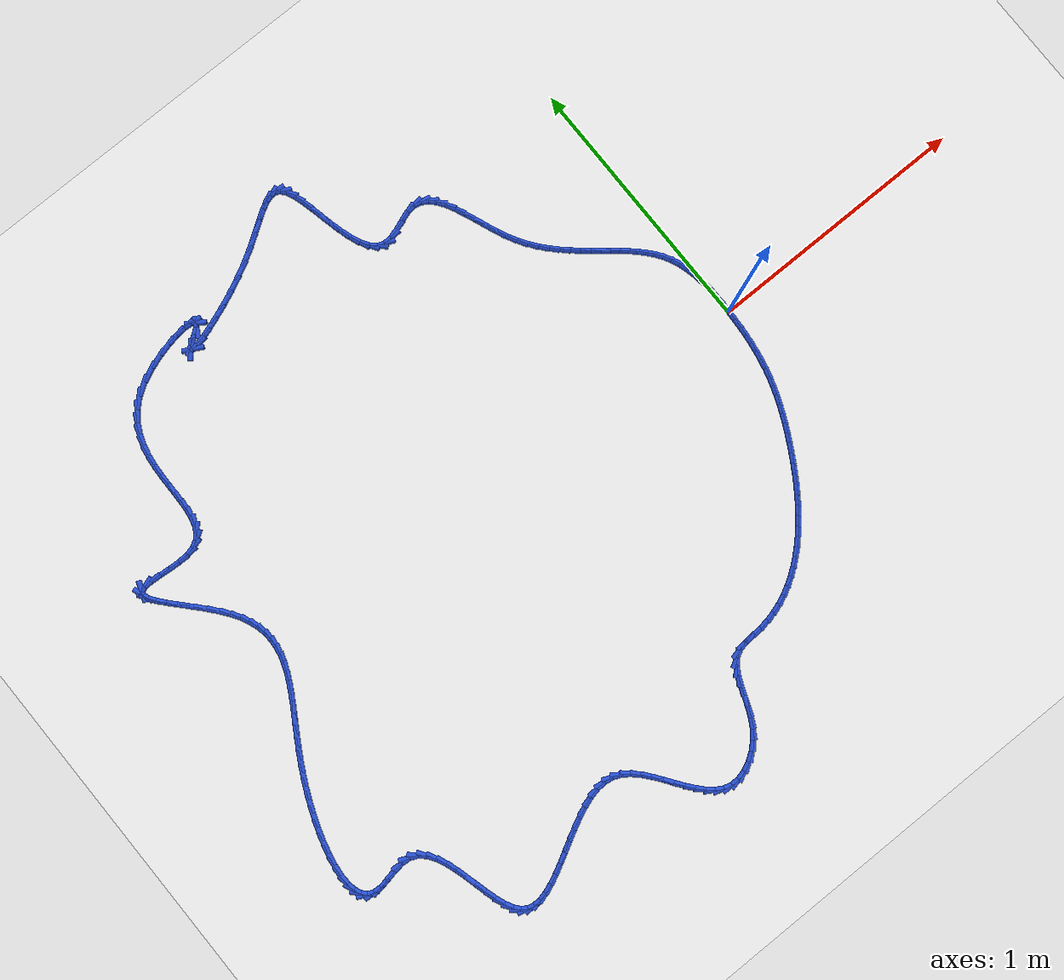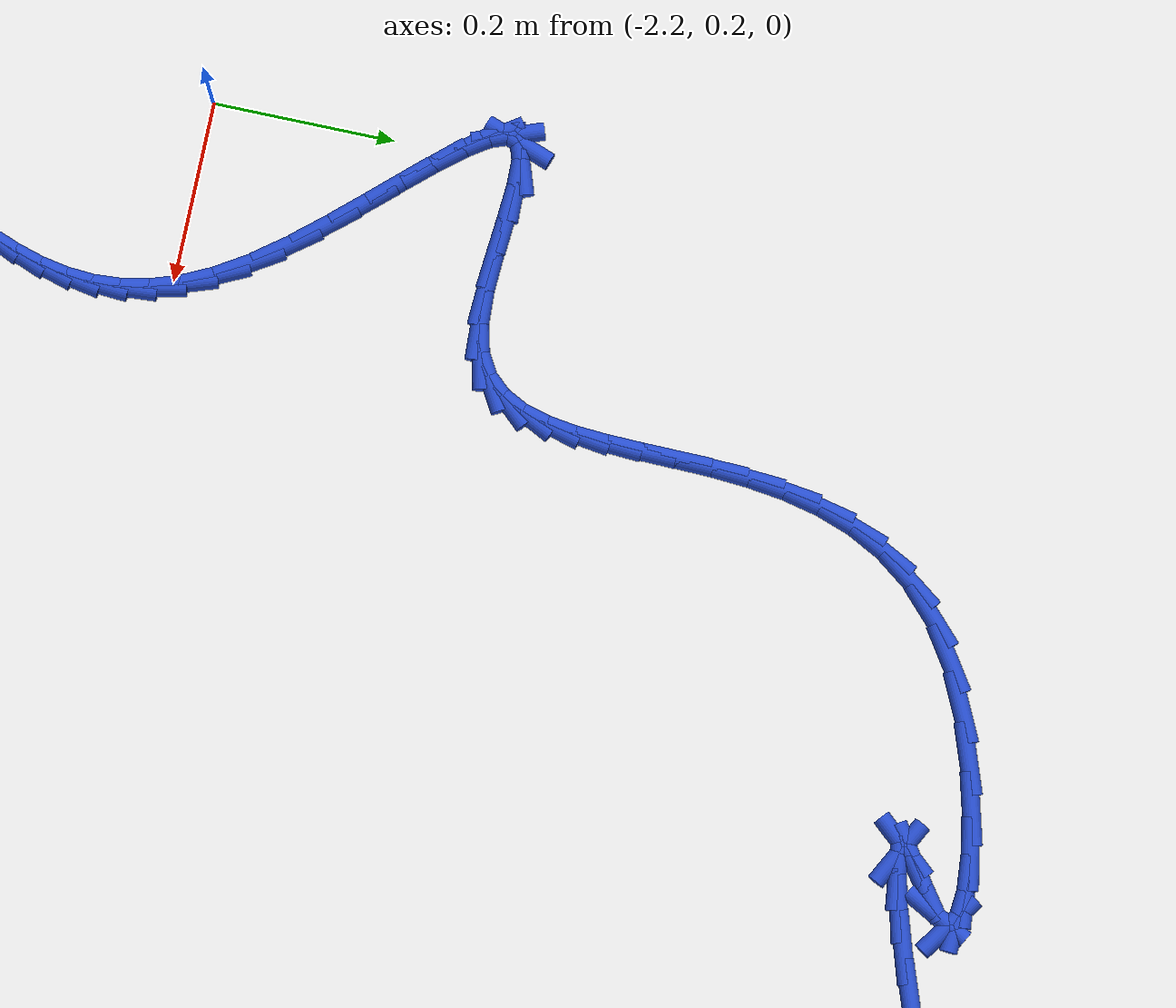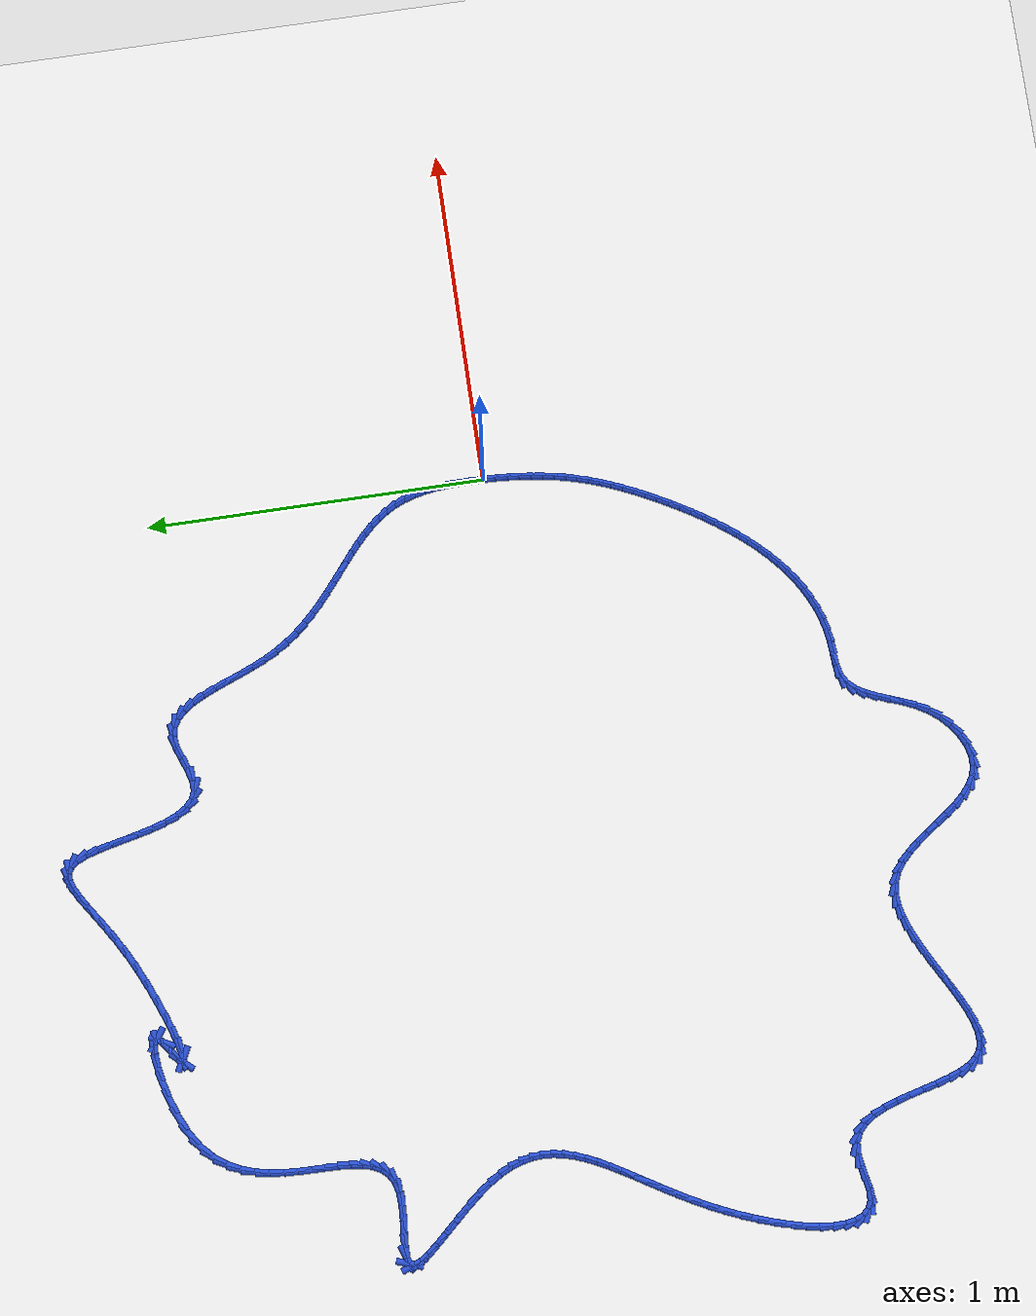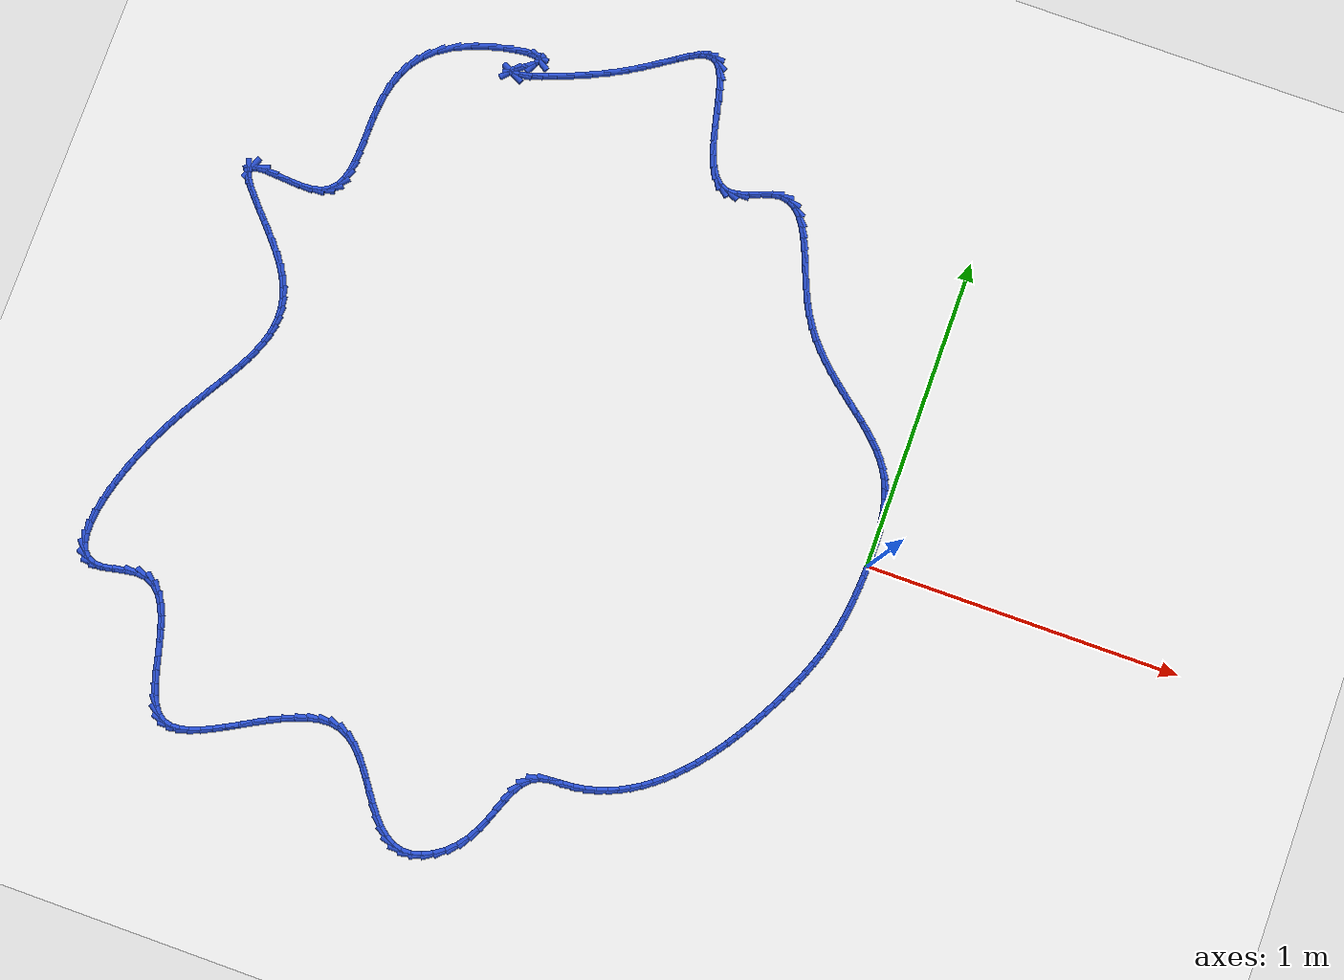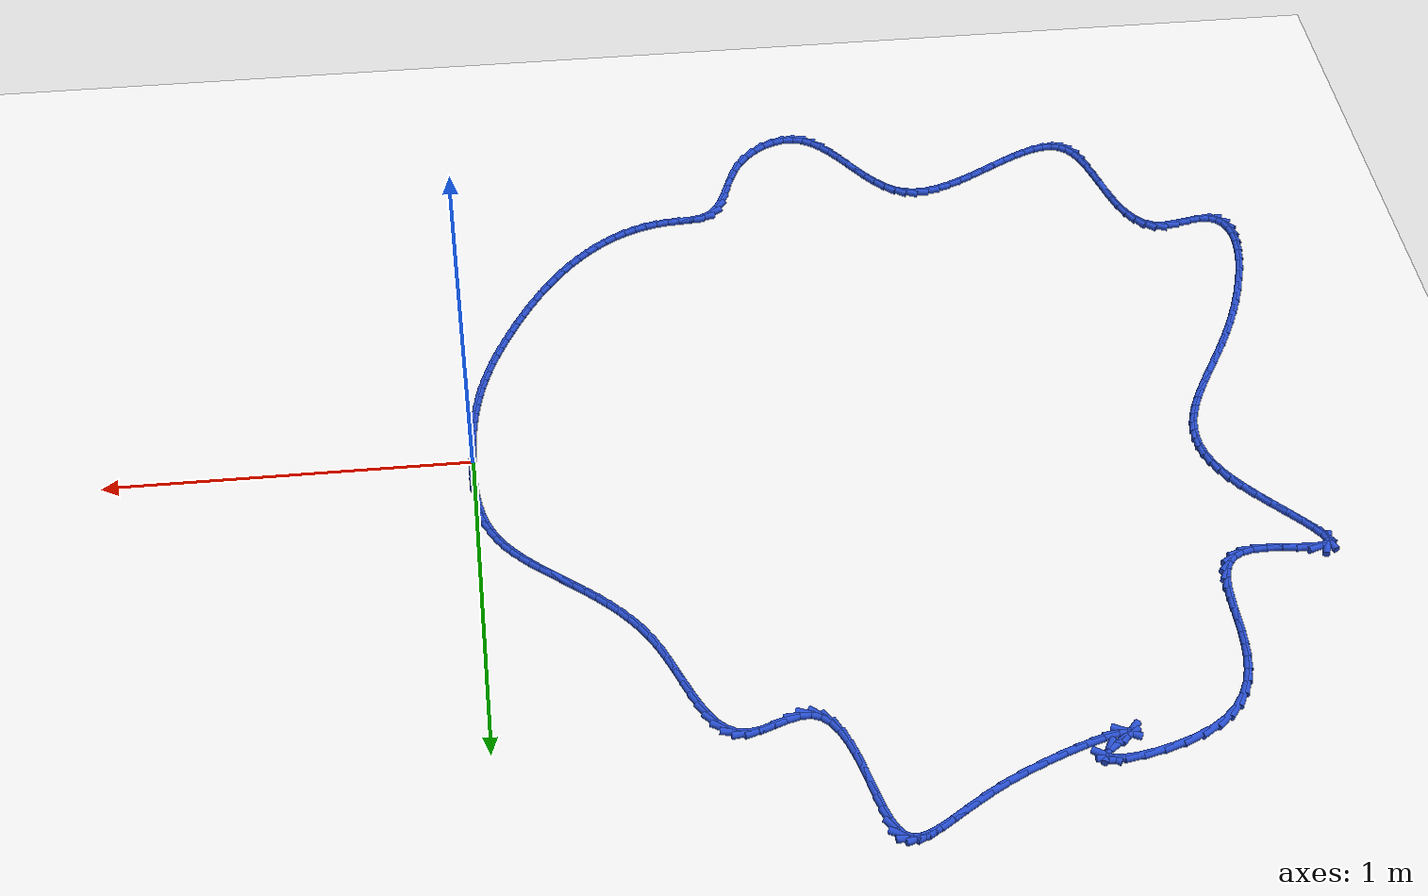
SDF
<sdf version="1.6">
 <world name="default">
  <light name="sun" type="directional">
   <pose>0 0 10 0 -0 0</pose>
   <diffuse>0.8 0.8 0.8 1</diffuse>
   <specular>0.2 0.2 0.2 1</specular>
   <attenuation>
    <range>1000</range>
    <constant>0.9</constant>
    <linear>0.01</linear>
    <quadratic>0.001</quadratic>
   </attenuation>
   <direction>-0.5 0.1 -0.9</direction>
  </light>
  <model name="ground_plane">
   <static>1</static>
   <link name="link">
    <collision name="collision">
     <geometry><plane><normal>0 0 1</normal><size>100 100</size></plane></geometry>
     <surface><friction><ode><mu>100</mu><mu2>50</mu2></ode></friction></surface>
    </collision>
    <visual name="visual">
     <cast_shadows>0</cast_shadows>
     <geometry><plane><normal>0 0 1</normal><size>100 100</size></plane></geometry>
     <material>
      <script><uri>file://media/materials/scripts/gazebo.material</uri><name>Gazebo/WhiteGlow</name></script>
     </material>
    </visual>
   </link>
  </model>
  <gravity>0 0 -9.8</gravity>
  <magnetic_field>6e-06 2.3e-05 -4.2e-05</magnetic_field>
  <atmosphere type="adiabatic"/>
  <physics name="default_physics" default="0" type="ode">
   <max_step_size>0.001</max_step_size>
   <real_time_factor>1</real_time_factor>
   <real_time_update_rate>1000</real_time_update_rate>
  </physics>
  <scene><ambient>0.4 0.4 0.4 1</ambient><background>0.7 0.7 0.7 1</background><shadows>1</shadows></scene>
  <spherical_coordinates>
   <surface_model>EARTH_WGS84</surface_model>
   <latitude_deg>0</latitude_deg>
   <longitude_deg>0</longitude_deg>
   <elevation>0</elevation>
   <heading_deg>0</heading_deg>
  </spherical_coordinates>
  <model name="line">
   <link name="link_0">
    <pose>1.496198998029996e-17 3.469446951953614e-17 0.01 0 1.57 1.5543776949053272</pose>
    <collision name="collision">
     <geometry><cylinder><radius>0.01</radius><length>0.08</length></cylinder></geometry>
    </collision>
    <visual name="visual">
     <material>
      <script><name>Gazebo/Blue</name><uri>file://media/materials/scripts/gazebo.material</uri></script>
     </material>
     <geometry><cylinder><radius>0.01</radius><length>0.08</length></cylinder></geometry>
    </visual>
   </link>
   <link name="link_1">
    <pose>0.0005924864957599677 0.03608298545428858 0.01 0 1.57 -1.559025904976044</pose>
    <collision name="collision">
     <geometry><cylinder><radius>0.01</radius><length>0.08</length></cylinder></geometry>
    </collision>
    <visual name="visual">
     <material>
      <script><name>Gazebo/Blue</name><uri>file://media/materials/scripts/gazebo.material</uri></script>
     </material>
     <geometry><cylinder><radius>0.01</radius><length>0.08</length></cylinder></geometry>
    </visual>
   </link>
   <link name="link_2">
    <pose>0.000166573687951816 0.07226632239206232 0.01 0 1.57 -1.522479859722978</pose>
    <collision name="collision">
     <geometry><cylinder><radius>0.01</radius><length>0.08</length></cylinder></geometry>
    </collision>
    <visual name="visual">
     <material>
      <script><name>Gazebo/Blue</name><uri>file://media/materials/scripts/gazebo.material</uri></script>
     </material>
     <geometry><cylinder><radius>0.01</radius><length>0.08</length></cylinder></geometry>
    </visual>
   </link>
   <link name="link_3">
    <pose>-0.0015710022527494825 0.10820072990928557 0.01 0 1.57 -1.4764854704934336</pose>
    <collision name="collision">
     <geometry><cylinder><radius>0.01</radius><length>0.08</length></cylinder></geometry>
    </collision>
    <visual name="visual">
     <material>
      <script><name>Gazebo/Blue</name><uri>file://media/materials/scripts/gazebo.material</uri></script>
     </material>
     <geometry><cylinder><radius>0.01</radius><length>0.08</length></cylinder></geometry>
    </visual>
   </link>
   <link name="link_4">
    <pose>-0.004913505155668969 0.14353692710192276 0.01 0 1.57 -1.4195641448092575</pose>
    <collision name="collision">
     <geometry><cylinder><radius>0.01</radius><length>0.08</length></cylinder></geometry>
    </collision>
    <visual name="visual">
     <material>
      <script><name>Gazebo/Blue</name><uri>file://media/materials/scripts/gazebo.material</uri></script>
     </material>
     <geometry><cylinder><radius>0.01</radius><length>0.08</length></cylinder></geometry>
    </visual>
   </link>
   <link name="link_5">
    <pose>-0.010154198850131687 0.17792563306593803 0.01 0 1.57 -1.3498712737847405</pose>
    <collision name="collision">
     <geometry><cylinder><radius>0.01</radius><length>0.08</length></cylinder></geometry>
    </collision>
    <visual name="visual">
     <material>
      <script><name>Gazebo/Blue</name><uri>file://media/materials/scripts/gazebo.material</uri></script>
     </material>
     <geometry><cylinder><radius>0.01</radius><length>0.08</length></cylinder></geometry>
    </visual>
   </link>
   <link name="link_6">
    <pose>-0.017586347165462694 0.2110175668972959 0.01 0 1.57 -1.2653053194806407</pose>
    <collision name="collision">
     <geometry><cylinder><radius>0.01</radius><length>0.08</length></cylinder></geometry>
    </collision>
    <visual name="visual">
     <material>
      <script><name>Gazebo/Blue</name><uri>file://media/materials/scripts/gazebo.material</uri></script>
     </material>
     <geometry><cylinder><radius>0.01</radius><length>0.08</length></cylinder></geometry>
    </visual>
   </link>
   <link name="link_7">
    <pose>-0.027503213930987015 0.24246344769196065 0.01 0 1.57 -1.1641971243596845</pose>
    <collision name="collision">
     <geometry><cylinder><radius>0.01</radius><length>0.08</length></cylinder></geometry>
    </collision>
    <visual name="visual">
     <material>
      <script><name>Gazebo/Blue</name><uri>file://media/materials/scripts/gazebo.material</uri></script>
     </material>
     <geometry><cylinder><radius>0.01</radius><length>0.08</length></cylinder></geometry>
    </visual>
   </link>
   <link name="link_8">
    <pose>-0.040188831175435036 0.2719241907529846 0.01 0 1.57 -1.0572484125708297</pose>
    <collision name="collision">
     <geometry><cylinder><radius>0.01</radius><length>0.08</length></cylinder></geometry>
    </collision>
    <visual name="visual">
     <material>
      <script><name>Gazebo/Blue</name><uri>file://media/materials/scripts/gazebo.material</uri></script>
     </material>
     <geometry><cylinder><radius>0.01</radius><length>0.08</length></cylinder></geometry>
    </visual>
   </link>
   <link name="link_9">
    <pose>-0.05566061919327846 0.2993551748986102 0.01 0 1.57 -0.9602683025920746</pose>
    <collision name="collision">
     <geometry><cylinder><radius>0.01</radius><length>0.08</length></cylinder></geometry>
    </collision>
    <visual name="visual">
     <material>
      <script><name>Gazebo/Blue</name><uri>file://media/materials/scripts/gazebo.material</uri></script>
     </material>
     <geometry><cylinder><radius>0.01</radius><length>0.08</length></cylinder></geometry>
    </visual>
   </link>
   <link name="link_10">
    <pose>-0.07363521219298796 0.32504398686152225 0.01 0 1.57 -0.876838987231082</pose>
    <collision name="collision">
     <geometry><cylinder><radius>0.01</radius><length>0.08</length></cylinder></geometry>
    </collision>
    <visual name="visual">
     <material>
      <script><name>Gazebo/Blue</name><uri>file://media/materials/scripts/gazebo.material</uri></script>
     </material>
     <geometry><cylinder><radius>0.01</radius><length>0.08</length></cylinder></geometry>
    </visual>
   </link>
   <link name="link_11">
    <pose>-0.09381314653134952 0.34929599289940366 0.01 0 1.57 -0.8083742009736272</pose>
    <collision name="collision">
     <geometry><cylinder><radius>0.01</radius><length>0.08</length></cylinder></geometry>
    </collision>
    <visual name="visual">
     <material>
      <script><name>Gazebo/Blue</name><uri>file://media/materials/scripts/gazebo.material</uri></script>
     </material>
     <geometry><cylinder><radius>0.01</radius><length>0.08</length></cylinder></geometry>
    </visual>
   </link>
   <link name="link_12">
    <pose>-0.11589495856514943 0.3724165592699378 0.01 0 1.57 -0.7551396467539171</pose>
    <collision name="collision">
     <geometry><cylinder><radius>0.01</radius><length>0.08</length></cylinder></geometry>
    </collision>
    <visual name="visual">
     <material>
      <script><name>Gazebo/Blue</name><uri>file://media/materials/scripts/gazebo.material</uri></script>
     </material>
     <geometry><cylinder><radius>0.01</radius><length>0.08</length></cylinder></geometry>
    </visual>
   </link>
   <link name="link_13">
    <pose>-0.13958118465117353 0.3947110522308071 0.01 0 1.57 -0.7167072337716769</pose>
    <collision name="collision">
     <geometry><cylinder><radius>0.01</radius><length>0.08</length></cylinder></geometry>
    </collision>
    <visual name="visual">
     <material>
      <script><name>Gazebo/Blue</name><uri>file://media/materials/scripts/gazebo.material</uri></script>
     </material>
     <geometry><cylinder><radius>0.01</radius><length>0.08</length></cylinder></geometry>
    </visual>
   </link>
   <link name="link_14">
    <pose>-0.16457236114620796 0.4164848380396951 0.01 0 1.57 -0.6923398217971319</pose>
    <collision name="collision">
     <geometry><cylinder><radius>0.01</radius><length>0.08</length></cylinder></geometry>
    </collision>
    <visual name="visual">
     <material>
      <script><name>Gazebo/Blue</name><uri>file://media/materials/scripts/gazebo.material</uri></script>
     </material>
     <geometry><cylinder><radius>0.01</radius><length>0.08</length></cylinder></geometry>
    </visual>
   </link>
   <link name="link_15">
    <pose>-0.1905690244070389 0.43804328295428463 0.01 0 1.57 -0.681244977231006</pose>
    <collision name="collision">
     <geometry><cylinder><radius>0.01</radius><length>0.08</length></cylinder></geometry>
    </collision>
    <visual name="visual">
     <material>
      <script><name>Gazebo/Blue</name><uri>file://media/materials/scripts/gazebo.material</uri></script>
     </material>
     <geometry><cylinder><radius>0.01</radius><length>0.08</length></cylinder></geometry>
    </visual>
   </link>
   <link name="link_16">
    <pose>-0.21727171079045235 0.4596917532322585 0.01 0 1.57 -0.6827074851305684</pose>
    <collision name="collision">
     <geometry><cylinder><radius>0.01</radius><length>0.08</length></cylinder></geometry>
    </collision>
    <visual name="visual">
     <material>
      <script><name>Gazebo/Blue</name><uri>file://media/materials/scripts/gazebo.material</uri></script>
     </material>
     <geometry><cylinder><radius>0.01</radius><length>0.08</length></cylinder></geometry>
    </visual>
   </link>
   <link name="link_17">
    <pose>-0.2443809566532343 0.4817356151313 0.01 0 1.57 -0.6961317074329647</pose>
    <collision name="collision">
     <geometry><cylinder><radius>0.01</radius><length>0.08</length></cylinder></geometry>
    </collision>
    <visual name="visual">
     <material>
      <script><name>Gazebo/Blue</name><uri>file://media/materials/scripts/gazebo.material</uri></script>
     </material>
     <geometry><cylinder><radius>0.01</radius><length>0.08</length></cylinder></geometry>
    </visual>
   </link>
   <link name="link_18">
    <pose>-0.27159729835217106 0.5044802349090921 0.01 0 1.57 -0.7210214999657552</pose>
    <collision name="collision">
     <geometry><cylinder><radius>0.01</radius><length>0.08</length></cylinder></geometry>
    </collision>
    <visual name="visual">
     <material>
      <script><name>Gazebo/Blue</name><uri>file://media/materials/scripts/gazebo.material</uri></script>
     </material>
     <geometry><cylinder><radius>0.01</radius><length>0.08</length></cylinder></geometry>
    </visual>
   </link>
   <link name="link_19">
    <pose>-0.29862127224404844 0.5282309788233176 0.01 0 1.57 -0.7569161711829396</pose>
    <collision name="collision">
     <geometry><cylinder><radius>0.01</radius><length>0.08</length></cylinder></geometry>
    </collision>
    <visual name="visual">
     <material>
      <script><name>Gazebo/Blue</name><uri>file://media/materials/scripts/gazebo.material</uri></script>
     </material>
     <geometry><cylinder><radius>0.01</radius><length>0.08</length></cylinder></geometry>
    </visual>
   </link>
   <link name="link_20">
    <pose>-0.32515341468565273 0.5532932131316598 0.01 0 1.57 -0.8032948544211704</pose>
    <collision name="collision">
     <geometry><cylinder><radius>0.01</radius><length>0.08</length></cylinder></geometry>
    </collision>
    <visual name="visual">
     <material>
      <script><name>Gazebo/Blue</name><uri>file://media/materials/scripts/gazebo.material</uri></script>
     </material>
     <geometry><cylinder><radius>0.01</radius><length>0.08</length></cylinder></geometry>
    </visual>
   </link>
   <link name="link_21">
    <pose>-0.35089426203377 0.5799723040918017 0.01 0 1.57 -0.8594619006583513</pose>
    <collision name="collision">
     <geometry><cylinder><radius>0.01</radius><length>0.08</length></cylinder></geometry>
    </collision>
    <visual name="visual">
     <material>
      <script><name>Gazebo/Blue</name><uri>file://media/materials/scripts/gazebo.material</uri></script>
     </material>
     <geometry><cylinder><radius>0.01</radius><length>0.08</length></cylinder></geometry>
    </visual>
   </link>
   <link name="link_22">
    <pose>-0.3755443506451862 0.6085736179614258 0.01 0 1.57 -0.9244326182334651</pose>
    <collision name="collision">
     <geometry><cylinder><radius>0.01</radius><length>0.08</length></cylinder></geometry>
    </collision>
    <visual name="visual">
     <material>
      <script><name>Gazebo/Blue</name><uri>file://media/materials/scripts/gazebo.material</uri></script>
     </material>
     <geometry><cylinder><radius>0.01</radius><length>0.08</length></cylinder></geometry>
    </visual>
   </link>
   <link name="link_23">
    <pose>-0.3988042168766873 0.6394025209982157 0.01 0 1.57 -0.9968487456268016</pose>
    <collision name="collision">
     <geometry><cylinder><radius>0.01</radius><length>0.08</length></cylinder></geometry>
    </collision>
    <visual name="visual">
     <material>
      <script><name>Gazebo/Blue</name><uri>file://media/materials/scripts/gazebo.material</uri></script>
     </material>
     <geometry><cylinder><radius>0.01</radius><length>0.08</length></cylinder></geometry>
    </visual>
   </link>
   <link name="link_24">
    <pose>-0.4203743970850598 0.6727643794598543 0.01 0 1.57 -1.0745203734010627</pose>
    <collision name="collision">
     <geometry><cylinder><radius>0.01</radius><length>0.08</length></cylinder></geometry>
    </collision>
    <visual name="visual">
     <material>
      <script><name>Gazebo/Blue</name><uri>file://media/materials/scripts/gazebo.material</uri></script>
     </material>
     <geometry><cylinder><radius>0.01</radius><length>0.08</length></cylinder></geometry>
    </visual>
   </link>
   <link name="link_25">
    <pose>-0.4399660477147284 0.7089462625246323 0.01 0 1.57 -1.1410847018998758</pose>
    <collision name="collision">
     <geometry><cylinder><radius>0.01</radius><length>0.08</length></cylinder></geometry>
    </collision>
    <visual name="visual">
     <material>
      <script><name>Gazebo/Blue</name><uri>file://media/materials/scripts/gazebo.material</uri></script>
     </material>
     <geometry><cylinder><radius>0.01</radius><length>0.08</length></cylinder></geometry>
    </visual>
   </link>
   <link name="link_26">
    <pose>-0.4576707358506095 0.7475798395354047 0.01 0 1.57 -1.1811009354069328</pose>
    <collision name="collision">
     <geometry><cylinder><radius>0.01</radius><length>0.08</length></cylinder></geometry>
    </collision>
    <visual name="visual">
     <material>
      <script><name>Gazebo/Blue</name><uri>file://media/materials/scripts/gazebo.material</uri></script>
     </material>
     <geometry><cylinder><radius>0.01</radius><length>0.08</length></cylinder></geometry>
    </visual>
   </link>
   <link name="link_27">
    <pose>-0.4740562041477041 0.7874763890334768 0.01 0 1.57 -1.1968618657690375</pose>
    <collision name="collision">
     <geometry><cylinder><radius>0.01</radius><length>0.08</length></cylinder></geometry>
    </collision>
    <visual name="visual">
     <material>
      <script><name>Gazebo/Blue</name><uri>file://media/materials/scripts/gazebo.material</uri></script>
     </material>
     <geometry><cylinder><radius>0.01</radius><length>0.08</length></cylinder></geometry>
    </visual>
   </link>
   <link name="link_28">
    <pose>-0.48972027154315895 0.8273953718971567 0.01 0 1.57 -1.1889511591006363</pose>
    <collision name="collision">
     <geometry><cylinder><radius>0.01</radius><length>0.08</length></cylinder></geometry>
    </collision>
    <visual name="visual">
     <material>
      <script><name>Gazebo/Blue</name><uri>file://media/materials/scripts/gazebo.material</uri></script>
     </material>
     <geometry><cylinder><radius>0.01</radius><length>0.08</length></cylinder></geometry>
    </visual>
   </link>
   <link name="link_29">
    <pose>-0.5052607569741215 0.8660962490047542 0.01 0 1.57 -1.1547153658933897</pose>
    <collision name="collision">
     <geometry><cylinder><radius>0.01</radius><length>0.08</length></cylinder></geometry>
    </collision>
    <visual name="visual">
     <material>
      <script><name>Gazebo/Blue</name><uri>file://media/materials/scripts/gazebo.material</uri></script>
     </material>
     <geometry><cylinder><radius>0.01</radius><length>0.08</length></cylinder></geometry>
    </visual>
   </link>
   <link name="link_30">
    <pose>-0.5212754793777384 0.9023384812345763 0.01 0 1.57 -1.0873089049267823</pose>
    <collision name="collision">
     <geometry><cylinder><radius>0.01</radius><length>0.08</length></cylinder></geometry>
    </collision>
    <visual name="visual">
     <material>
      <script><name>Gazebo/Blue</name><uri>file://media/materials/scripts/gazebo.material</uri></script>
     </material>
     <geometry><cylinder><radius>0.01</radius><length>0.08</length></cylinder></geometry>
    </visual>
   </link>
   <link name="link_31">
    <pose>-0.5383622576911572 0.9348815294649326 0.01 0 1.57 -0.97395685003428</pose>
    <collision name="collision">
     <geometry><cylinder><radius>0.01</radius><length>0.08</length></cylinder></geometry>
    </collision>
    <visual name="visual">
     <material>
      <script><name>Gazebo/Blue</name><uri>file://media/materials/scripts/gazebo.material</uri></script>
     </material>
     <geometry><cylinder><radius>0.01</radius><length>0.08</length></cylinder></geometry>
    </visual>
   </link>
   <link name="link_32">
    <pose>-0.5571189108515248 0.9624848545741316 0.01 0 1.57 -0.7947910615229079</pose>
    <collision name="collision">
     <geometry><cylinder><radius>0.01</radius><length>0.08</length></cylinder></geometry>
    </collision>
    <visual name="visual">
     <material>
      <script><name>Gazebo/Blue</name><uri>file://media/materials/scripts/gazebo.material</uri></script>
     </material>
     <geometry><cylinder><radius>0.01</radius><length>0.08</length></cylinder></geometry>
    </visual>
   </link>
   <link name="link_33">
    <pose>-0.5781432577959882 0.9839079174404813 0.01 0 1.57 -0.5301491335337567</pose>
    <collision name="collision">
     <geometry><cylinder><radius>0.01</radius><length>0.08</length></cylinder></geometry>
    </collision>
    <visual name="visual">
     <material>
      <script><name>Gazebo/Blue</name><uri>file://media/materials/scripts/gazebo.material</uri></script>
     </material>
     <geometry><cylinder><radius>0.01</radius><length>0.08</length></cylinder></geometry>
    </visual>
   </link>
   <link name="link_34">
    <pose>-0.6020331174616944 0.9979101789422908 0.01 0 1.57 -0.19283151795735634</pose>
    <collision name="collision">
     <geometry><cylinder><radius>0.01</radius><length>0.08</length></cylinder></geometry>
    </collision>
    <visual name="visual">
     <material>
      <script><name>Gazebo/Blue</name><uri>file://media/materials/scripts/gazebo.material</uri></script>
     </material>
     <geometry><cylinder><radius>0.01</radius><length>0.08</length></cylinder></geometry>
    </visual>
   </link>
   <link name="link_35">
    <pose>-0.629386308785791 1.0032510999578688 0.01 0 1.57 0.13594427644705256</pose>
    <collision name="collision">
     <geometry><cylinder><radius>0.01</radius><length>0.08</length></cylinder></geometry>
    </collision>
    <visual name="visual">
     <material>
      <script><name>Gazebo/Blue</name><uri>file://media/materials/scripts/gazebo.material</uri></script>
     </material>
     <geometry><cylinder><radius>0.01</radius><length>0.08</length></cylinder></geometry>
    </visual>
   </link>
   <link name="link_36">
    <pose>-0.6606825223082821 0.9989701544743113 0.01 0 1.57 0.31854672344433616</pose>
    <collision name="collision">
     <geometry><cylinder><radius>0.01</radius><length>0.08</length></cylinder></geometry>
    </collision>
    <visual name="visual">
     <material>
      <script><name>Gazebo/Blue</name><uri>file://media/materials/scripts/gazebo.material</uri></script>
     </material>
     <geometry><cylinder><radius>0.01</radius><length>0.08</length></cylinder></geometry>
    </visual>
   </link>
   <link name="link_37">
    <pose>-0.6948901320491382 0.9876892610676105 0.01 0 1.57 0.3598006952621342</pose>
    <collision name="collision">
     <geometry><cylinder><radius>0.01</radius><length>0.08</length></cylinder></geometry>
    </collision>
    <visual name="visual">
     <material>
      <script><name>Gazebo/Blue</name><uri>file://media/materials/scripts/gazebo.material</uri></script>
     </material>
     <geometry><cylinder><radius>0.01</radius><length>0.08</length></cylinder></geometry>
    </visual>
   </link>
   <link name="link_38">
    <pose>-0.7299326312458763 0.9745071374855544 0.01 0 1.57 0.2860495755884501</pose>
    <collision name="collision">
     <geometry><cylinder><radius>0.01</radius><length>0.08</length></cylinder></geometry>
    </collision>
    <visual name="visual">
     <material>
      <script><name>Gazebo/Blue</name><uri>file://media/materials/scripts/gazebo.material</uri></script>
     </material>
     <geometry><cylinder><radius>0.01</radius><length>0.08</length></cylinder></geometry>
    </visual>
   </link>
   <link name="link_39">
    <pose>-0.7637126737853487 0.9645718993472794 0.01 0 1.57 0.05087276005107938</pose>
    <collision name="collision">
     <geometry><cylinder><radius>0.01</radius><length>0.08</length></cylinder></geometry>
    </collision>
    <visual name="visual">
     <material>
      <script><name>Gazebo/Blue</name><uri>file://media/materials/scripts/gazebo.material</uri></script>
     </material>
     <geometry><cylinder><radius>0.01</radius><length>0.08</length></cylinder></geometry>
    </visual>
   </link>
   <link name="link_40">
    <pose>-0.7941363638452923 0.963022825678673 0.01 0 1.57 -0.370664362213738</pose>
    <collision name="collision">
     <geometry><cylinder><radius>0.01</radius><length>0.08</length></cylinder></geometry>
    </collision>
    <visual name="visual">
     <material>
      <script><name>Gazebo/Blue</name><uri>file://media/materials/scripts/gazebo.material</uri></script>
     </material>
     <geometry><cylinder><radius>0.01</radius><length>0.08</length></cylinder></geometry>
    </visual>
   </link>
   <link name="link_41">
    <pose>-0.8198797029675283 0.9730273994817381 0.01 0 1.57 -0.756689813008445</pose>
    <collision name="collision">
     <geometry><cylinder><radius>0.01</radius><length>0.08</length></cylinder></geometry>
    </collision>
    <visual name="visual">
     <material>
      <script><name>Gazebo/Blue</name><uri>file://media/materials/scripts/gazebo.material</uri></script>
     </material>
     <geometry><cylinder><radius>0.01</radius><length>0.08</length></cylinder></geometry>
    </visual>
   </link>
   <link name="link_42">
    <pose>-0.8413557057962646 0.9933044126880638 0.01 0 1.57 -1.0135000549010977</pose>
    <collision name="collision">
     <geometry><cylinder><radius>0.01</radius><length>0.08</length></cylinder></geometry>
    </collision>
    <visual name="visual">
     <material>
      <script><name>Gazebo/Blue</name><uri>file://media/materials/scripts/gazebo.material</uri></script>
     </material>
     <geometry><cylinder><radius>0.01</radius><length>0.08</length></cylinder></geometry>
    </visual>
   </link>
   <link name="link_43">
    <pose>-0.859215432090175 1.0219629962119348 0.01 0 1.57 -1.169984914363689</pose>
    <collision name="collision">
     <geometry><cylinder><radius>0.01</radius><length>0.08</length></cylinder></geometry>
    </collision>
    <visual name="visual">
     <material>
      <script><name>Gazebo/Blue</name><uri>file://media/materials/scripts/gazebo.material</uri></script>
     </material>
     <geometry><cylinder><radius>0.01</radius><length>0.08</length></cylinder></geometry>
    </visual>
   </link>
   <link name="link_44">
    <pose>-0.8741099416079333 1.0571122809676345 0.01 0 1.57 -1.2642770482631147</pose>
    <collision name="collision">
     <geometry><cylinder><radius>0.01</radius><length>0.08</length></cylinder></geometry>
    </collision>
    <visual name="visual">
     <material>
      <script><name>Gazebo/Blue</name><uri>file://media/materials/scripts/gazebo.material</uri></script>
     </material>
     <geometry><cylinder><radius>0.01</radius><length>0.08</length></cylinder></geometry>
    </visual>
   </link>
   <link name="link_45">
    <pose>-0.8866902941082132 1.0968613978694477 0.01 0 1.57 -1.3191182128599988</pose>
    <collision name="collision">
     <geometry><cylinder><radius>0.01</radius><length>0.08</length></cylinder></geometry>
    </collision>
    <visual name="visual">
     <material>
      <script><name>Gazebo/Blue</name><uri>file://media/materials/scripts/gazebo.material</uri></script>
     </material>
     <geometry><cylinder><radius>0.01</radius><length>0.08</length></cylinder></geometry>
    </visual>
   </link>
   <link name="link_46">
    <pose>-0.8976075493496877 1.1393194778316573 0.01 0 1.57 -1.3457882595074597</pose>
    <collision name="collision">
     <geometry><cylinder><radius>0.01</radius><length>0.08</length></cylinder></geometry>
    </collision>
    <visual name="visual">
     <material>
      <script><name>Gazebo/Blue</name><uri>file://media/materials/scripts/gazebo.material</uri></script>
     </material>
     <geometry><cylinder><radius>0.01</radius><length>0.08</length></cylinder></geometry>
    </visual>
   </link>
   <link name="link_47">
    <pose>-0.907512767091031 1.1825956517685485 0.01 0 1.57 -1.3483888897992953</pose>
    <collision name="collision">
     <geometry><cylinder><radius>0.01</radius><length>0.08</length></cylinder></geometry>
    </collision>
    <visual name="visual">
     <material>
      <script><name>Gazebo/Blue</name><uri>file://media/materials/scripts/gazebo.material</uri></script>
     </material>
     <geometry><cylinder><radius>0.01</radius><length>0.08</length></cylinder></geometry>
    </visual>
   </link>
   <link name="link_48">
    <pose>-0.9170570070909165 1.2247990505944046 0.01 0 1.57 -1.325232907538848</pose>
    <collision name="collision">
     <geometry><cylinder><radius>0.01</radius><length>0.08</length></cylinder></geometry>
    </collision>
    <visual name="visual">
     <material>
      <script><name>Gazebo/Blue</name><uri>file://media/materials/scripts/gazebo.material</uri></script>
     </material>
     <geometry><cylinder><radius>0.01</radius><length>0.08</length></cylinder></geometry>
    </visual>
   </link>
   <link name="link_49">
    <pose>-0.9268913291080181 1.2640388052235099 0.01 0 1.57 -1.267114801058829</pose>
    <collision name="collision">
     <geometry><cylinder><radius>0.01</radius><length>0.08</length></cylinder></geometry>
    </collision>
    <visual name="visual">
     <material>
      <script><name>Gazebo/Blue</name><uri>file://media/materials/scripts/gazebo.material</uri></script>
     </material>
     <geometry><cylinder><radius>0.01</radius><length>0.08</length></cylinder></geometry>
    </visual>
   </link>
   <link name="link_50">
    <pose>-0.937666792901009 1.2984240465701482 0.01 0 1.57 -1.1500586619250919</pose>
    <collision name="collision">
     <geometry><cylinder><radius>0.01</radius><length>0.08</length></cylinder></geometry>
    </collision>
    <visual name="visual">
     <material>
      <script><name>Gazebo/Blue</name><uri>file://media/materials/scripts/gazebo.material</uri></script>
     </material>
     <geometry><cylinder><radius>0.01</radius><length>0.08</length></cylinder></geometry>
    </visual>
   </link>
   <link name="link_51">
    <pose>-0.9500344582285629 1.3260639055486036 0.01 0 1.57 -0.9153413898617649</pose>
    <collision name="collision">
     <geometry><cylinder><radius>0.01</radius><length>0.08</length></cylinder></geometry>
    </collision>
    <visual name="visual">
     <material>
      <script><name>Gazebo/Blue</name><uri>file://media/materials/scripts/gazebo.material</uri></script>
     </material>
     <geometry><cylinder><radius>0.01</radius><length>0.08</length></cylinder></geometry>
    </visual>
   </link>
   <link name="link_52">
    <pose>-0.9646453780004289 1.345067564115056 0.01 0 1.57 -0.480618907367325</pose>
    <collision name="collision">
     <geometry><cylinder><radius>0.01</radius><length>0.08</length></cylinder></geometry>
    </collision>
    <visual name="visual">
     <material>
      <script><name>Gazebo/Blue</name><uri>file://media/materials/scripts/gazebo.material</uri></script>
     </material>
     <geometry><cylinder><radius>0.01</radius><length>0.08</length></cylinder></geometry>
    </visual>
   </link>
   <link name="link_53">
    <pose>-0.9820690211093458 1.3541522124492258 0.01 0 1.57 -0.0001650352604188273</pose>
    <collision name="collision">
     <geometry><cylinder><radius>0.01</radius><length>0.08</length></cylinder></geometry>
    </collision>
    <visual name="visual">
     <material>
      <script><name>Gazebo/Blue</name><uri>file://media/materials/scripts/gazebo.material</uri></script>
     </material>
     <geometry><cylinder><radius>0.01</radius><length>0.08</length></cylinder></geometry>
    </visual>
   </link>
   <link name="link_54">
    <pose>-1.002590314775097 1.3541555991863008 0.01 0 1.57 0.31535034359079633</pose>
    <collision name="collision">
     <geometry><cylinder><radius>0.01</radius><length>0.08</length></cylinder></geometry>
    </collision>
    <visual name="visual">
     <material>
      <script><name>Gazebo/Blue</name><uri>file://media/materials/scripts/gazebo.material</uri></script>
     </material>
     <geometry><cylinder><radius>0.01</radius><length>0.08</length></cylinder></geometry>
    </visual>
   </link>
   <link name="link_55">
    <pose>-1.0264321907989364 1.3463774963536679 0.01 0 1.57 0.48007725752422425</pose>
    <collision name="collision">
     <geometry><cylinder><radius>0.01</radius><length>0.08</length></cylinder></geometry>
    </collision>
    <visual name="visual">
     <material>
      <script><name>Gazebo/Blue</name><uri>file://media/materials/scripts/gazebo.material</uri></script>
     </material>
     <geometry><cylinder><radius>0.01</radius><length>0.08</length></cylinder></geometry>
    </visual>
   </link>
   <link name="link_56">
    <pose>-1.0538175809821186 1.3321176759787123 0.01 0 1.57 0.5579496667024882</pose>
    <collision name="collision">
     <geometry><cylinder><radius>0.01</radius><length>0.08</length></cylinder></geometry>
    </collision>
    <visual name="visual">
     <material>
      <script><name>Gazebo/Blue</name><uri>file://media/materials/scripts/gazebo.material</uri></script>
     </material>
     <geometry><cylinder><radius>0.01</radius><length>0.08</length></cylinder></geometry>
    </visual>
   </link>
   <link name="link_57">
    <pose>-1.0849694171258972 1.3126759100888201 0.01 0 1.57 0.5859600827256446</pose>
    <collision name="collision">
     <geometry><cylinder><radius>0.01</radius><length>0.08</length></cylinder></geometry>
    </collision>
    <visual name="visual">
     <material>
      <script><name>Gazebo/Blue</name><uri>file://media/materials/scripts/gazebo.material</uri></script>
     </material>
     <geometry><cylinder><radius>0.01</radius><length>0.08</length></cylinder></geometry>
    </visual>
   </link>
   <link name="link_58">
    <pose>-1.1201106310315265 1.2893519707113767 0.01 0 1.57 0.5821864242988005</pose>
    <collision name="collision">
     <geometry><cylinder><radius>0.01</radius><length>0.08</length></cylinder></geometry>
    </collision>
    <visual name="visual">
     <material>
      <script><name>Gazebo/Blue</name><uri>file://media/materials/scripts/gazebo.material</uri></script>
     </material>
     <geometry><cylinder><radius>0.01</radius><length>0.08</length></cylinder></geometry>
    </visual>
   </link>
   <link name="link_59">
    <pose>-1.1594641545002602 1.2634456298737695 0.01 0 1.57 0.5556542393024929</pose>
    <collision name="collision">
     <geometry><cylinder><radius>0.01</radius><length>0.08</length></cylinder></geometry>
    </collision>
    <visual name="visual">
     <material>
      <script><name>Gazebo/Blue</name><uri>file://media/materials/scripts/gazebo.material</uri></script>
     </material>
     <geometry><cylinder><radius>0.01</radius><length>0.08</length></cylinder></geometry>
    </visual>
   </link>
   <link name="link_60">
    <pose>-1.2032529193333525 1.2362566596033826 0.01 0 1.57 0.5112071678785837</pose>
    <collision name="collision">
     <geometry><cylinder><radius>0.01</radius><length>0.08</length></cylinder></geometry>
    </collision>
    <visual name="visual">
     <material>
      <script><name>Gazebo/Blue</name><uri>file://media/materials/scripts/gazebo.material</uri></script>
     </material>
     <geometry><cylinder><radius>0.01</radius><length>0.08</length></cylinder></geometry>
    </visual>
   </link>
   <link name="link_61">
    <pose>-1.2516941934568433 1.2090837857300907 0.01 0 1.57 0.46053968597940514</pose>
    <collision name="collision">
     <geometry><cylinder><radius>0.01</radius><length>0.08</length></cylinder></geometry>
    </collision>
    <visual name="visual">
     <material>
      <script><name>Gazebo/Blue</name><uri>file://media/materials/scripts/gazebo.material</uri></script>
     </material>
     <geometry><cylinder><radius>0.01</radius><length>0.08</length></cylinder></geometry>
    </visual>
   </link>
   <link name="link_62">
    <pose>-1.3041376539338914 1.1830654778337149 0.01 0 1.57 0.41908297755803303</pose>
    <collision name="collision">
     <geometry><cylinder><radius>0.01</radius><length>0.08</length></cylinder></geometry>
    </collision>
    <visual name="visual">
     <material>
      <script><name>Gazebo/Blue</name><uri>file://media/materials/scripts/gazebo.material</uri></script>
     </material>
     <geometry><cylinder><radius>0.01</radius><length>0.08</length></cylinder></geometry>
    </visual>
   </link>
   <link name="link_63">
    <pose>-1.3581397911256947 1.1590089786580244 0.01 0 1.57 0.383279070164344</pose>
    <collision name="collision">
     <geometry><cylinder><radius>0.01</radius><length>0.08</length></cylinder></geometry>
    </collision>
    <visual name="visual">
     <material>
      <script><name>Gazebo/Blue</name><uri>file://media/materials/scripts/gazebo.material</uri></script>
     </material>
     <geometry><cylinder><radius>0.01</radius><length>0.08</length></cylinder></geometry>
    </visual>
   </link>
   <link name="link_64">
    <pose>-1.4110351205067233 1.137680529059293 0.01 0 1.57 0.34825375251334034</pose>
    <collision name="collision">
     <geometry><cylinder><radius>0.01</radius><length>0.08</length></cylinder></geometry>
    </collision>
    <visual name="visual">
     <material>
      <script><name>Gazebo/Blue</name><uri>file://media/materials/scripts/gazebo.material</uri></script>
     </material>
     <geometry><cylinder><radius>0.01</radius><length>0.08</length></cylinder></geometry>
    </visual>
   </link>
   <link name="link_65">
    <pose>-1.4601581575514486 1.119846369893794 0.01 0 1.57 0.3078816084806811</pose>
    <collision name="collision">
     <geometry><cylinder><radius>0.01</radius><length>0.08</length></cylinder></geometry>
    </collision>
    <visual name="visual">
     <material>
      <script><name>Gazebo/Blue</name><uri>file://media/materials/scripts/gazebo.material</uri></script>
     </material>
     <geometry><cylinder><radius>0.01</radius><length>0.08</length></cylinder></geometry>
    </visual>
   </link>
   <link name="link_66">
    <pose>-1.502843417734342 1.1062727420178 0.01 0 1.57 0.2492160813838277</pose>
    <collision name="collision">
     <geometry><cylinder><radius>0.01</radius><length>0.08</length></cylinder></geometry>
    </collision>
    <visual name="visual">
     <material>
      <script><name>Gazebo/Blue</name><uri>file://media/materials/scripts/gazebo.material</uri></script>
     </material>
     <geometry><cylinder><radius>0.01</radius><length>0.08</length></cylinder></geometry>
    </visual>
   </link>
   <link name="link_67">
    <pose>-1.5364254165298727 1.0977258862875852 0.01 0 1.57 0.12558194365086814</pose>
    <collision name="collision">
     <geometry><cylinder><radius>0.01</radius><length>0.08</length></cylinder></geometry>
    </collision>
    <visual name="visual">
     <material>
      <script><name>Gazebo/Blue</name><uri>file://media/materials/scripts/gazebo.material</uri></script>
     </material>
     <geometry><cylinder><radius>0.01</radius><length>0.08</length></cylinder></geometry>
    </visual>
   </link>
   <link name="link_68">
    <pose>-1.558238669412513 1.0949720435594226 0.01 0 1.57 -0.4761338491387476</pose>
    <collision name="collision">
     <geometry><cylinder><radius>0.01</radius><length>0.08</length></cylinder></geometry>
    </collision>
    <visual name="visual">
     <material>
      <script><name>Gazebo/Blue</name><uri>file://media/materials/scripts/gazebo.material</uri></script>
     </material>
     <geometry><cylinder><radius>0.01</radius><length>0.08</length></cylinder></geometry>
    </visual>
   </link>
   <link name="link_69">
    <pose>-1.5656176918567333 1.0987774546895857 0.01 0 1.57 0.8529262781482487</pose>
    <collision name="collision">
     <geometry><cylinder><radius>0.01</radius><length>0.08</length></cylinder></geometry>
    </collision>
    <visual name="visual">
     <material>
      <script><name>Gazebo/Blue</name><uri>file://media/materials/scripts/gazebo.material</uri></script>
     </material>
     <geometry><cylinder><radius>0.01</radius><length>0.08</length></cylinder></geometry>
    </visual>
   </link>
   <link name="link_70">
    <pose>-1.5558969993370042 1.1099083605343472 0.01 0 1.57 0.595841687415803</pose>
    <collision name="collision">
     <geometry><cylinder><radius>0.01</radius><length>0.08</length></cylinder></geometry>
    </collision>
    <visual name="visual">
     <material>
      <script><name>Gazebo/Blue</name><uri>file://media/materials/scripts/gazebo.material</uri></script>
     </material>
     <geometry><cylinder><radius>0.01</radius><length>0.08</length></cylinder></geometry>
    </visual>
   </link>
   <link name="link_71">
    <pose>-1.5286377466025152 1.1283914834487074 0.01 0 1.57 0.6294370940099295</pose>
    <collision name="collision">
     <geometry><cylinder><radius>0.01</radius><length>0.08</length></cylinder></geometry>
    </collision>
    <visual name="visual">
     <material>
      <script><name>Gazebo/Blue</name><uri>file://media/materials/scripts/gazebo.material</uri></script>
     </material>
     <geometry><cylinder><radius>0.01</radius><length>0.08</length></cylinder></geometry>
    </visual>
   </link>
   <link name="link_72">
    <pose>-1.5012784057374926 1.148316003634057 0.01 0 1.57 1.08370847268191</pose>
    <collision name="collision">
     <geometry><cylinder><radius>0.01</radius><length>0.08</length></cylinder></geometry>
    </collision>
    <visual name="visual">
     <material>
      <script><name>Gazebo/Blue</name><uri>file://media/materials/scripts/gazebo.material</uri></script>
     </material>
     <geometry><cylinder><radius>0.01</radius><length>0.08</length></cylinder></geometry>
    </visual>
   </link>
   <link name="link_73">
    <pose>-1.4936017450227885 1.1628097508448605 0.01 0 1.57 -0.5970294302344263</pose>
    <collision name="collision">
     <geometry><cylinder><radius>0.01</radius><length>0.08</length></cylinder></geometry>
    </collision>
    <visual name="visual">
     <material>
      <script><name>Gazebo/Blue</name><uri>file://media/materials/scripts/gazebo.material</uri></script>
     </material>
     <geometry><cylinder><radius>0.01</radius><length>0.08</length></cylinder></geometry>
    </visual>
   </link>
   <link name="link_74">
    <pose>-1.5056288193814804 1.1709855721664628 0.01 0 1.57 -0.0772614202629387</pose>
    <collision name="collision">
     <geometry><cylinder><radius>0.01</radius><length>0.08</length></cylinder></geometry>
    </collision>
    <visual name="visual">
     <material>
      <script><name>Gazebo/Blue</name><uri>file://media/materials/scripts/gazebo.material</uri></script>
     </material>
     <geometry><cylinder><radius>0.01</radius><length>0.08</length></cylinder></geometry>
    </visual>
   </link>
   <link name="link_75">
    <pose>-1.5334702829819002 1.1731409335798426 0.01 0 1.57 0.08947496645256169</pose>
    <collision name="collision">
     <geometry><cylinder><radius>0.01</radius><length>0.08</length></cylinder></geometry>
    </collision>
    <visual name="visual">
     <material>
      <script><name>Gazebo/Blue</name><uri>file://media/materials/scripts/gazebo.material</uri></script>
     </material>
     <geometry><cylinder><radius>0.01</radius><length>0.08</length></cylinder></geometry>
    </visual>
   </link>
   <link name="link_76">
    <pose>-1.5732367899923816 1.169573301065979 0.01 0 1.57 0.18595914539488775</pose>
    <collision name="collision">
     <geometry><cylinder><radius>0.01</radius><length>0.08</length></cylinder></geometry>
    </collision>
    <visual name="visual">
     <material>
      <script><name>Gazebo/Blue</name><uri>file://media/materials/scripts/gazebo.material</uri></script>
     </material>
     <geometry><cylinder><radius>0.01</radius><length>0.08</length></cylinder></geometry>
    </visual>
   </link>
   <link name="link_77">
    <pose>-1.6210389945812567 1.1605801406058518 0.01 0 1.57 0.26541753619041364</pose>
    <collision name="collision">
     <geometry><cylinder><radius>0.01</radius><length>0.08</length></cylinder></geometry>
    </collision>
    <visual name="visual">
     <material>
      <script><name>Gazebo/Blue</name><uri>file://media/materials/scripts/gazebo.material</uri></script>
     </material>
     <geometry><cylinder><radius>0.01</radius><length>0.08</length></cylinder></geometry>
    </visual>
   </link>
   <link name="link_78">
    <pose>-1.67298755091686 1.1464589181804385 0.01 0 1.57 0.3482291430202658</pose>
    <collision name="collision">
     <geometry><cylinder><radius>0.01</radius><length>0.08</length></cylinder></geometry>
    </collision>
    <visual name="visual">
     <material>
      <script><name>Gazebo/Blue</name><uri>file://media/materials/scripts/gazebo.material</uri></script>
     </material>
     <geometry><cylinder><radius>0.01</radius><length>0.08</length></cylinder></geometry>
    </visual>
   </link>
   <link name="link_79">
    <pose>-1.7251931131675233 1.1275070997707197 0.01 0 1.57 0.45035727830083616</pose>
    <collision name="collision">
     <geometry><cylinder><radius>0.01</radius><length>0.08</length></cylinder></geometry>
    </collision>
    <visual name="visual">
     <material>
      <script><name>Gazebo/Blue</name><uri>file://media/materials/scripts/gazebo.material</uri></script>
     </material>
     <geometry><cylinder><radius>0.01</radius><length>0.08</length></cylinder></geometry>
    </visual>
   </link>
   <link name="link_80">
    <pose>-1.7737663355015796 1.1040221513576738 0.01 0 1.57 0.591687997035373</pose>
    <collision name="collision">
     <geometry><cylinder><radius>0.01</radius><length>0.08</length></cylinder></geometry>
    </collision>
    <visual name="visual">
     <material>
      <script><name>Gazebo/Blue</name><uri>file://media/materials/scripts/gazebo.material</uri></script>
     </material>
     <geometry><cylinder><radius>0.01</radius><length>0.08</length></cylinder></geometry>
    </visual>
   </link>
   <link name="link_81">
    <pose>-1.8149994211370908 1.076313387995146 0.01 0 1.57 0.7639928992509496</pose>
    <collision name="collision">
     <geometry><cylinder><radius>0.01</radius><length>0.08</length></cylinder></geometry>
    </collision>
    <visual name="visual">
     <material>
      <script><name>Gazebo/Blue</name><uri>file://media/materials/scripts/gazebo.material</uri></script>
     </material>
     <geometry><cylinder><radius>0.01</radius><length>0.08</length></cylinder></geometry>
    </visual>
   </link>
   <link name="link_82">
    <pose>-1.8478263573905844 1.0448625447652125 0.01 0 1.57 0.9382066611999026</pose>
    <collision name="collision">
     <geometry><cylinder><radius>0.01</radius><length>0.08</length></cylinder></geometry>
    </collision>
    <visual name="visual">
     <material>
      <script><name>Gazebo/Blue</name><uri>file://media/materials/scripts/gazebo.material</uri></script>
     </material>
     <geometry><cylinder><radius>0.01</radius><length>0.08</length></cylinder></geometry>
    </visual>
   </link>
   <link name="link_83">
    <pose>-1.8731772279396504 1.010281634993022 0.01 0 1.57 1.1005663036138182</pose>
    <collision name="collision">
     <geometry><cylinder><radius>0.01</radius><length>0.08</length></cylinder></geometry>
    </collision>
    <visual name="visual">
     <material>
      <script><name>Gazebo/Blue</name><uri>file://media/materials/scripts/gazebo.material</uri></script>
     </material>
     <geometry><cylinder><radius>0.01</radius><length>0.08</length></cylinder></geometry>
    </visual>
   </link>
   <link name="link_84">
    <pose>-1.892031339915804 0.9731858846467707 0.01 0 1.57 1.241260515323911</pose>
    <collision name="collision">
     <geometry><cylinder><radius>0.01</radius><length>0.08</length></cylinder></geometry>
    </collision>
    <visual name="visual">
     <material>
      <script><name>Gazebo/Blue</name><uri>file://media/materials/scripts/gazebo.material</uri></script>
     </material>
     <geometry><cylinder><radius>0.01</radius><length>0.08</length></cylinder></geometry>
    </visual>
   </link>
   <link name="link_85">
    <pose>-1.9053680004505613 0.9341905196946535 0.01 0 1.57 1.35573906647768</pose>
    <collision name="collision">
     <geometry><cylinder><radius>0.01</radius><length>0.08</length></cylinder></geometry>
    </collision>
    <visual name="visual">
     <material>
      <script><name>Gazebo/Blue</name><uri>file://media/materials/scripts/gazebo.material</uri></script>
     </material>
     <geometry><cylinder><radius>0.01</radius><length>0.08</length></cylinder></geometry>
    </visual>
   </link>
   <link name="link_86">
    <pose>-1.9141665166754374 0.8939107661048671 0.01 0 1.57 1.443531406932914</pose>
    <collision name="collision">
     <geometry><cylinder><radius>0.01</radius><length>0.08</length></cylinder></geometry>
    </collision>
    <visual name="visual">
     <material>
      <script><name>Gazebo/Blue</name><uri>file://media/materials/scripts/gazebo.material</uri></script>
     </material>
     <geometry><cylinder><radius>0.01</radius><length>0.08</length></cylinder></geometry>
    </visual>
   </link>
   <link name="link_87">
    <pose>-1.9194061957219477 0.8529618498456066 0.01 0 1.57 1.5060099528140576</pose>
    <collision name="collision">
     <geometry><cylinder><radius>0.01</radius><length>0.08</length></cylinder></geometry>
    </collision>
    <visual name="visual">
     <material>
      <script><name>Gazebo/Blue</name><uri>file://media/materials/scripts/gazebo.material</uri></script>
     </material>
     <geometry><cylinder><radius>0.01</radius><length>0.08</length></cylinder></geometry>
    </visual>
   </link>
   <link name="link_88">
    <pose>-1.922066344721608 0.8119589968850682 0.01 0 1.57 1.5445934948866262</pose>
    <collision name="collision">
     <geometry><cylinder><radius>0.01</radius><length>0.08</length></cylinder></geometry>
    </collision>
    <visual name="visual">
     <material>
      <script><name>Gazebo/Blue</name><uri>file://media/materials/scripts/gazebo.material</uri></script>
     </material>
     <geometry><cylinder><radius>0.01</radius><length>0.08</length></cylinder></geometry>
    </visual>
   </link>
   <link name="link_89">
    <pose>-1.9231262708059351 0.7715174331914472 0.01 0 1.57 1.5596161035206093</pose>
    <collision name="collision">
     <geometry><cylinder><radius>0.01</radius><length>0.08</length></cylinder></geometry>
    </collision>
    <visual name="visual">
     <material>
      <script><name>Gazebo/Blue</name><uri>file://media/materials/scripts/gazebo.material</uri></script>
     </material>
     <geometry><cylinder><radius>0.01</radius><length>0.08</length></cylinder></geometry>
    </visual>
   </link>
   <link name="link_90">
    <pose>-1.9235652811064436 0.7322523847329401 0.01 0 1.57 1.5495203470708574</pose>
    <collision name="collision">
     <geometry><cylinder><radius>0.01</radius><length>0.08</length></cylinder></geometry>
    </collision>
    <visual name="visual">
     <material>
      <script><name>Gazebo/Blue</name><uri>file://media/materials/scripts/gazebo.material</uri></script>
     </material>
     <geometry><cylinder><radius>0.01</radius><length>0.08</length></cylinder></geometry>
    </visual>
   </link>
   <link name="link_91">
    <pose>-1.9243626827546496 0.6947790774777421 0.01 0 1.57 1.5099839493675415</pose>
    <collision name="collision">
     <geometry><cylinder><radius>0.01</radius><length>0.08</length></cylinder></geometry>
    </collision>
    <visual name="visual">
     <material>
      <script><name>Gazebo/Blue</name><uri>file://media/materials/scripts/gazebo.material</uri></script>
     </material>
     <geometry><cylinder><radius>0.01</radius><length>0.08</length></cylinder></geometry>
    </visual>
   </link>
   <link name="link_92">
    <pose>-1.926497782882068 0.659712737394049 0.01 0 1.57 1.432743467348962</pose>
    <collision name="collision">
     <geometry><cylinder><radius>0.01</radius><length>0.08</length></cylinder></geometry>
    </collision>
    <visual name="visual">
     <material>
      <script><name>Gazebo/Blue</name><uri>file://media/materials/scripts/gazebo.material</uri></script>
     </material>
     <geometry><cylinder><radius>0.01</radius><length>0.08</length></cylinder></geometry>
    </visual>
   </link>
   <link name="link_93">
    <pose>-1.9309498886202157 0.6276685904500567 0.01 0 1.57 1.3045072831148112</pose>
    <collision name="collision">
     <geometry><cylinder><radius>0.01</radius><length>0.08</length></cylinder></geometry>
    </collision>
    <visual name="visual">
     <material>
      <script><name>Gazebo/Blue</name><uri>file://media/materials/scripts/gazebo.material</uri></script>
     </material>
     <geometry><cylinder><radius>0.01</radius><length>0.08</length></cylinder></geometry>
    </visual>
   </link>
   <link name="link_94">
    <pose>-1.9386983071006072 0.5992618626139611 0.01 0 1.57 1.108905755260092</pose>
    <collision name="collision">
     <geometry><cylinder><radius>0.01</radius><length>0.08</length></cylinder></geometry>
    </collision>
    <visual name="visual">
     <material>
      <script><name>Gazebo/Blue</name><uri>file://media/materials/scripts/gazebo.material</uri></script>
     </material>
     <geometry><cylinder><radius>0.01</radius><length>0.08</length></cylinder></geometry>
    </visual>
   </link>
   <link name="link_95">
    <pose>-1.9507223454547589 0.5751077798539578 0.01 0 1.57 0.8402381477647437</pose>
    <collision name="collision">
     <geometry><cylinder><radius>0.01</radius><length>0.08</length></cylinder></geometry>
    </collision>
    <visual name="visual">
     <material>
      <script><name>Gazebo/Blue</name><uri>file://media/materials/scripts/gazebo.material</uri></script>
     </material>
     <geometry><cylinder><radius>0.01</radius><length>0.08</length></cylinder></geometry>
    </visual>
   </link>
   <link name="link_96">
    <pose>-1.9680013108141865 0.5558215681382425 0.01 0 1.57 0.5308332444847561</pose>
    <collision name="collision">
     <geometry><cylinder><radius>0.01</radius><length>0.08</length></cylinder></geometry>
    </collision>
    <visual name="visual">
     <material>
      <script><name>Gazebo/Blue</name><uri>file://media/materials/scripts/gazebo.material</uri></script>
     </material>
     <geometry><cylinder><radius>0.01</radius><length>0.08</length></cylinder></geometry>
    </visual>
   </link>
   <link name="link_97">
    <pose>-1.9915145103104053 0.5420184534350112 0.01 0 1.57 0.2459315151775736</pose>
    <collision name="collision">
     <geometry><cylinder><radius>0.01</radius><length>0.08</length></cylinder></geometry>
    </collision>
    <visual name="visual">
     <material>
      <script><name>Gazebo/Blue</name><uri>file://media/materials/scripts/gazebo.material</uri></script>
     </material>
     <geometry><cylinder><radius>0.01</radius><length>0.08</length></cylinder></geometry>
    </visual>
   </link>
   <link name="link_98">
    <pose>-2.0222321061903066 0.5343079483887585 0.01 0 1.57 0.050211833476726926</pose>
    <collision name="collision">
     <geometry><cylinder><radius>0.01</radius><length>0.08</length></cylinder></geometry>
    </collision>
    <visual name="visual">
     <material>
      <script><name>Gazebo/Blue</name><uri>file://media/materials/scripts/gazebo.material</uri></script>
     </material>
     <geometry><cylinder><radius>0.01</radius><length>0.08</length></cylinder></geometry>
    </visual>
   </link>
   <link name="link_99">
    <pose>-2.0597226428694095 0.5324238961626595 0.01 0 1.57 -0.04555569203650313</pose>
    <collision name="collision">
     <geometry><cylinder><radius>0.01</radius><length>0.08</length></cylinder></geometry>
    </collision>
    <visual name="visual">
     <material>
      <script><name>Gazebo/Blue</name><uri>file://media/materials/scripts/gazebo.material</uri></script>
     </material>
     <geometry><cylinder><radius>0.01</radius><length>0.08</length></cylinder></geometry>
    </visual>
   </link>
   <link name="link_100">
    <pose>-2.1006573011702905 0.5342899939458274 0.01 0 1.57 -0.08130797092445677</pose>
    <collision name="collision">
     <geometry><cylinder><radius>0.01</radius><length>0.08</length></cylinder></geometry>
    </collision>
    <visual name="visual">
     <material>
      <script><name>Gazebo/Blue</name><uri>file://media/materials/scripts/gazebo.material</uri></script>
     </material>
     <geometry><cylinder><radius>0.01</radius><length>0.08</length></cylinder></geometry>
    </visual>
   </link>
   <link name="link_101">
    <pose>-2.141348541899856 0.5376058263604369 0.01 0 1.57 -0.06695993671499163</pose>
    <collision name="collision">
     <geometry><cylinder><radius>0.01</radius><length>0.08</length></cylinder></geometry>
    </collision>
    <visual name="visual">
     <material>
      <script><name>Gazebo/Blue</name><uri>file://media/materials/scripts/gazebo.material</uri></script>
     </material>
     <geometry><cylinder><radius>0.01</radius><length>0.08</length></cylinder></geometry>
    </visual>
   </link>
   <link name="link_102">
    <pose>-2.178108825865015 0.5400709780286622 0.01 0 1.57 0.02353382765656031</pose>
    <collision name="collision">
     <geometry><cylinder><radius>0.01</radius><length>0.08</length></cylinder></geometry>
    </collision>
    <visual name="visual">
     <material>
      <script><name>Gazebo/Blue</name><uri>file://media/materials/scripts/gazebo.material</uri></script>
     </material>
     <geometry><cylinder><radius>0.01</radius><length>0.08</length></cylinder></geometry>
    </visual>
   </link>
   <link name="link_103">
    <pose>-2.207250613872679 0.5393850335726786 0.01 0 1.57 0.33092880955815523</pose>
    <collision name="collision">
     <geometry><cylinder><radius>0.01</radius><length>0.08</length></cylinder></geometry>
    </collision>
    <visual name="visual">
     <material>
      <script><name>Gazebo/Blue</name><uri>file://media/materials/scripts/gazebo.material</uri></script>
     </material>
     <geometry><cylinder><radius>0.01</radius><length>0.08</length></cylinder></geometry>
    </visual>
   </link>
   <link name="link_104">
    <pose>-2.2250972439251266 0.5332535921931708 0.01 0 1.57 1.2271412205592238</pose>
    <collision name="collision">
     <geometry><cylinder><radius>0.01</radius><length>0.08</length></cylinder></geometry>
    </collision>
    <visual name="visual">
     <material>
      <script><name>Gazebo/Blue</name><uri>file://media/materials/scripts/gazebo.material</uri></script>
     </material>
     <geometry><cylinder><radius>0.01</radius><length>0.08</length></cylinder></geometry>
    </visual>
   </link>
   <link name="link_105">
    <pose>-2.2297160677361085 0.5203466108167064 0.01 0 1.57 -1.2225862500264042</pose>
    <collision name="collision">
     <geometry><cylinder><radius>0.01</radius><length>0.08</length></cylinder></geometry>
    </collision>
    <visual name="visual">
     <material>
      <script><name>Gazebo/Blue</name><uri>file://media/materials/scripts/gazebo.material</uri></script>
     </material>
     <geometry><cylinder><radius>0.01</radius><length>0.08</length></cylinder></geometry>
    </visual>
   </link>
   <link name="link_106">
    <pose>-2.22282028139576 0.5013500271896137 0.01 0 1.57 -0.9787455630980134</pose>
    <collision name="collision">
     <geometry><cylinder><radius>0.01</radius><length>0.08</length></cylinder></geometry>
    </collision>
    <visual name="visual">
     <material>
      <script><name>Gazebo/Blue</name><uri>file://media/materials/scripts/gazebo.material</uri></script>
     </material>
     <geometry><cylinder><radius>0.01</radius><length>0.08</length></cylinder></geometry>
    </visual>
   </link>
   <link name="link_107">
    <pose>-2.2065804835024925 0.47720270117677743 0.01 0 1.57 -0.8806425585426093</pose>
    <collision name="collision">
     <geometry><cylinder><radius>0.01</radius><length>0.08</length></cylinder></geometry>
    </collision>
    <visual name="visual">
     <material>
      <script><name>Gazebo/Blue</name><uri>file://media/materials/scripts/gazebo.material</uri></script>
     </material>
     <geometry><cylinder><radius>0.01</radius><length>0.08</length></cylinder></geometry>
    </visual>
   </link>
   <link name="link_108">
    <pose>-2.1831672726547176 0.4488434926430814 0.01 0 1.57 -0.8389073909016722</pose>
    <collision name="collision">
     <geometry><cylinder><radius>0.01</radius><length>0.08</length></cylinder></geometry>
    </collision>
    <visual name="visual">
     <material>
      <script><name>Gazebo/Blue</name><uri>file://media/materials/scripts/gazebo.material</uri></script>
     </material>
     <geometry><cylinder><radius>0.01</radius><length>0.08</length></cylinder></geometry>
    </visual>
   </link>
   <link name="link_109">
    <pose>-2.1547512474508497 0.4172112614534111 0.01 0 1.57 -0.82705416039861</pose>
    <collision name="collision">
     <geometry><cylinder><radius>0.01</radius><length>0.08</length></cylinder></geometry>
    </collision>
    <visual name="visual">
     <material>
      <script><name>Gazebo/Blue</name><uri>file://media/materials/scripts/gazebo.material</uri></script>
     </material>
     <geometry><cylinder><radius>0.01</radius><length>0.08</length></cylinder></geometry>
    </visual>
   </link>
   <link name="link_110">
    <pose>-2.1235030064892997 0.3832448674726504 0.01 0 1.57 -0.8366652121062161</pose>
    <collision name="collision">
     <geometry><cylinder><radius>0.01</radius><length>0.08</length></cylinder></geometry>
    </collision>
    <visual name="visual">
     <material>
      <script><name>Gazebo/Blue</name><uri>file://media/materials/scripts/gazebo.material</uri></script>
     </material>
     <geometry><cylinder><radius>0.01</radius><length>0.08</length></cylinder></geometry>
    </visual>
   </link>
   <link name="link_111">
    <pose>-2.0915931483684793 0.34788317056568385 0.01 0 1.57 -0.8670246610117589</pose>
    <collision name="collision">
     <geometry><cylinder><radius>0.01</radius><length>0.08</length></cylinder></geometry>
    </collision>
    <visual name="visual">
     <material>
      <script><name>Gazebo/Blue</name><uri>file://media/materials/scripts/gazebo.material</uri></script>
     </material>
     <geometry><cylinder><radius>0.01</radius><length>0.08</length></cylinder></geometry>
    </visual>
   </link>
   <link name="link_112">
    <pose>-2.0611922716868016 0.3120650305973953 0.01 0 1.57 -0.9233305796120584</pose>
    <collision name="collision">
     <geometry><cylinder><radius>0.01</radius><length>0.08</length></cylinder></geometry>
    </collision>
    <visual name="visual">
     <material>
      <script><name>Gazebo/Blue</name><uri>file://media/materials/scripts/gazebo.material</uri></script>
     </material>
     <geometry><cylinder><radius>0.01</radius><length>0.08</length></cylinder></geometry>
    </visual>
   </link>
   <link name="link_113">
    <pose>-2.0344709060041555 0.276729276423202 0.01 0 1.57 -1.011573168788963</pose>
    <collision name="collision">
     <geometry><cylinder><radius>0.01</radius><length>0.08</length></cylinder></geometry>
    </collision>
    <visual name="visual">
     <material>
      <script><name>Gazebo/Blue</name><uri>file://media/materials/scripts/gazebo.material</uri></script>
     </material>
     <geometry><cylinder><radius>0.01</radius><length>0.08</length></cylinder></geometry>
    </visual>
   </link>
   <link name="link_114">
    <pose>-2.0131061835406148 0.24259312165650496 0.01 0 1.57 -1.1188501569619445</pose>
    <collision name="collision">
     <geometry><cylinder><radius>0.01</radius><length>0.08</length></cylinder></geometry>
    </collision>
    <visual name="visual">
     <material>
      <script><name>Gazebo/Blue</name><uri>file://media/materials/scripts/gazebo.material</uri></script>
     </material>
     <geometry><cylinder><radius>0.01</radius><length>0.08</length></cylinder></geometry>
    </visual>
   </link>
   <link name="link_115">
    <pose>-1.9970997120923155 0.2096211983283774 0.01 0 1.57 -1.2396714154995376</pose>
    <collision name="collision">
     <geometry><cylinder><radius>0.01</radius><length>0.08</length></cylinder></geometry>
    </collision>
    <visual name="visual">
     <material>
      <script><name>Gazebo/Blue</name><uri>file://media/materials/scripts/gazebo.material</uri></script>
     </material>
     <geometry><cylinder><radius>0.01</radius><length>0.08</length></cylinder></geometry>
    </visual>
   </link>
   <link name="link_116">
    <pose>-1.986097765018199 0.1776185358110622 0.01 0 1.57 -1.370155258010546</pose>
    <collision name="collision">
     <geometry><cylinder><radius>0.01</radius><length>0.08</length></cylinder></geometry>
    </collision>
    <visual name="visual">
     <material>
      <script><name>Gazebo/Blue</name><uri>file://media/materials/scripts/gazebo.material</uri></script>
     </material>
     <geometry><cylinder><radius>0.01</radius><length>0.08</length></cylinder></geometry>
    </visual>
   </link>
   <link name="link_117">
    <pose>-1.9797466156772068 0.14639016347680078 0.01 0 1.57 -1.5038770921991265</pose>
    <collision name="collision">
     <geometry><cylinder><radius>0.01</radius><length>0.08</length></cylinder></geometry>
    </collision>
    <visual name="visual">
     <material>
      <script><name>Gazebo/Blue</name><uri>file://media/materials/scripts/gazebo.material</uri></script>
     </material>
     <geometry><cylinder><radius>0.01</radius><length>0.08</length></cylinder></geometry>
    </visual>
   </link>
   <link name="link_118">
    <pose>-1.9776925374282797 0.11574111069783503 0.01 0 1.57 1.5084524865155196</pose>
    <collision name="collision">
     <geometry><cylinder><radius>0.01</radius><length>0.08</length></cylinder></geometry>
    </collision>
    <visual name="visual">
     <material>
      <script><name>Gazebo/Blue</name><uri>file://media/materials/scripts/gazebo.material</uri></script>
     </material>
     <geometry><cylinder><radius>0.01</radius><length>0.08</length></cylinder></geometry>
    </visual>
   </link>
   <link name="link_119">
    <pose>-1.97958180363036 0.08547640684640649 0.01 0 1.57 1.3906002942337556</pose>
    <collision name="collision">
     <geometry><cylinder><radius>0.01</radius><length>0.08</length></cylinder></geometry>
    </collision>
    <visual name="visual">
     <material>
      <script><name>Gazebo/Blue</name><uri>file://media/materials/scripts/gazebo.material</uri></script>
     </material>
     <geometry><cylinder><radius>0.01</radius><length>0.08</length></cylinder></geometry>
    </visual>
   </link>
   <link name="link_120">
    <pose>-1.9850606876423893 0.055401081294757897 0.01 0 1.57 1.2888054329643657</pose>
    <collision name="collision">
     <geometry><cylinder><radius>0.01</radius><length>0.08</length></cylinder></geometry>
    </collision>
    <visual name="visual">
     <material>
      <script><name>Gazebo/Blue</name><uri>file://media/materials/scripts/gazebo.material</uri></script>
     </material>
     <geometry><cylinder><radius>0.01</radius><length>0.08</length></cylinder></geometry>
    </visual>
   </link>
   <link name="link_121">
    <pose>-1.9937754628233084 0.025320163415130617 0.01 0 1.57 1.20505545254791</pose>
    <collision name="collision">
     <geometry><cylinder><radius>0.01</radius><length>0.08</length></cylinder></geometry>
    </collision>
    <visual name="visual">
     <material>
      <script><name>Gazebo/Blue</name><uri>file://media/materials/scripts/gazebo.material</uri></script>
     </material>
     <geometry><cylinder><radius>0.01</radius><length>0.08</length></cylinder></geometry>
    </visual>
   </link>
   <link name="link_122">
    <pose>-2.005372402532059 -0.004961317420233313 0.01 0 1.57 1.139282304859191</pose>
    <collision name="collision">
     <geometry><cylinder><radius>0.01</radius><length>0.08</length></cylinder></geometry>
    </collision>
    <visual name="visual">
     <material>
      <script><name>Gazebo/Blue</name><uri>file://media/materials/scripts/gazebo.material</uri></script>
     </material>
     <geometry><cylinder><radius>0.01</radius><length>0.08</length></cylinder></geometry>
    </visual>
   </link>
   <link name="link_123">
    <pose>-2.019497780127583 -0.03563833183909207 0.01 0 1.57 1.0902459461408651</pose>
    <collision name="collision">
     <geometry><cylinder><radius>0.01</radius><length>0.08</length></cylinder></geometry>
    </collision>
    <visual name="visual">
     <material>
      <script><name>Gazebo/Blue</name><uri>file://media/materials/scripts/gazebo.material</uri></script>
     </material>
     <geometry><cylinder><radius>0.01</radius><length>0.08</length></cylinder></geometry>
    </visual>
   </link>
   <link name="link_124">
    <pose>-2.035797868968822 -0.06690585046920372 0.01 0 1.57 1.0562465609551452</pose>
    <collision name="collision">
     <geometry><cylinder><radius>0.01</radius><length>0.08</length></cylinder></geometry>
    </collision>
    <visual name="visual">
     <material>
      <script><name>Gazebo/Blue</name><uri>file://media/materials/scripts/gazebo.material</uri></script>
     </material>
     <geometry><cylinder><radius>0.01</radius><length>0.08</length></cylinder></geometry>
    </visual>
   </link>
   <link name="link_125">
    <pose>-2.0539189424147173 -0.09895884393832724 0.01 0 1.57 1.0355509349282706</pose>
    <collision name="collision">
     <geometry><cylinder><radius>0.01</radius><length>0.08</length></cylinder></geometry>
    </collision>
    <visual name="visual">
     <material>
      <script><name>Gazebo/Blue</name><uri>file://media/materials/scripts/gazebo.material</uri></script>
     </material>
     <geometry><cylinder><radius>0.01</radius><length>0.08</length></cylinder></geometry>
    </visual>
   </link>
   <link name="link_126">
    <pose>-2.07350727382421 -0.13199228287421902 0.01 0 1.57 1.0265906593864178</pose>
    <collision name="collision">
     <geometry><cylinder><radius>0.01</radius><length>0.08</length></cylinder></geometry>
    </collision>
    <visual name="visual">
     <material>
      <script><name>Gazebo/Blue</name><uri>file://media/materials/scripts/gazebo.material</uri></script>
     </material>
     <geometry><cylinder><radius>0.01</radius><length>0.08</length></cylinder></geometry>
    </visual>
   </link>
   <link name="link_127">
    <pose>-2.094209136556242 -0.16620113790463797 0.01 0 1.57 1.028021667607654</pose>
    <collision name="collision">
     <geometry><cylinder><radius>0.01</radius><length>0.08</length></cylinder></geometry>
    </collision>
    <visual name="visual">
     <material>
      <script><name>Gazebo/Blue</name><uri>file://media/materials/scripts/gazebo.material</uri></script>
     </material>
     <geometry><cylinder><radius>0.01</radius><length>0.08</length></cylinder></geometry>
    </visual>
   </link>
   <link name="link_128">
    <pose>-2.1156708039697554 -0.20178037965734227 0.01 0 1.57 1.0387126914129479</pose>
    <collision name="collision">
     <geometry><cylinder><radius>0.01</radius><length>0.08</length></cylinder></geometry>
    </collision>
    <visual name="visual">
     <material>
      <script><name>Gazebo/Blue</name><uri>file://media/materials/scripts/gazebo.material</uri></script>
     </material>
     <geometry><cylinder><radius>0.01</radius><length>0.08</length></cylinder></geometry>
    </visual>
   </link>
   <link name="link_129">
    <pose>-2.13753854942369 -0.23892497876008992 0.01 0 1.57 1.057702750596362</pose>
    <collision name="collision">
     <geometry><cylinder><radius>0.01</radius><length>0.08</length></cylinder></geometry>
    </collision>
    <visual name="visual">
     <material>
      <script><name>Gazebo/Blue</name><uri>file://media/materials/scripts/gazebo.material</uri></script>
     </material>
     <geometry><cylinder><radius>0.01</radius><length>0.08</length></cylinder></geometry>
    </visual>
   </link>
   <link name="link_130">
    <pose>-2.1594586462769882 -0.27782990584063905 0.01 0 1.57 1.0841487433224002</pose>
    <collision name="collision">
     <geometry><cylinder><radius>0.01</radius><length>0.08</length></cylinder></geometry>
    </collision>
    <visual name="visual">
     <material>
      <script><name>Gazebo/Blue</name><uri>file://media/materials/scripts/gazebo.material</uri></script>
     </material>
     <geometry><cylinder><radius>0.01</radius><length>0.08</length></cylinder></geometry>
    </visual>
   </link>
   <link name="link_131">
    <pose>-2.181077367888592 -0.31869013152674774 0.01 0 1.57 1.117265813266629</pose>
    <collision name="collision">
     <geometry><cylinder><radius>0.01</radius><length>0.08</length></cylinder></geometry>
    </collision>
    <visual name="visual">
     <material>
      <script><name>Gazebo/Blue</name><uri>file://media/materials/scripts/gazebo.material</uri></script>
     </material>
     <geometry><cylinder><radius>0.01</radius><length>0.08</length></cylinder></geometry>
    </visual>
   </link>
   <link name="link_132">
    <pose>-2.202040873680242 -0.3616995302147877 0.01 0 1.57 1.154455870545464</pose>
    <collision name="collision">
     <geometry><cylinder><radius>0.01</radius><length>0.08</length></cylinder></geometry>
    </collision>
    <visual name="visual">
     <material>
      <script><name>Gazebo/Blue</name><uri>file://media/materials/scripts/gazebo.material</uri></script>
     </material>
     <geometry><cylinder><radius>0.01</radius><length>0.08</length></cylinder></geometry>
    </visual>
   </link>
   <link name="link_133">
    <pose>-2.2219646072618624 -0.4067564482681402 0.01 0 1.57 1.1920858337775488</pose>
    <collision name="collision">
     <geometry><cylinder><radius>0.01</radius><length>0.08</length></cylinder></geometry>
    </collision>
    <visual name="visual">
     <material>
      <script><name>Gazebo/Blue</name><uri>file://media/materials/scripts/gazebo.material</uri></script>
     </material>
     <geometry><cylinder><radius>0.01</radius><length>0.08</length></cylinder></geometry>
    </visual>
   </link>
   <link name="link_134">
    <pose>-2.2403919386705096 -0.4530657859075429 0.01 0 1.57 1.2316340818287375</pose>
    <collision name="collision">
     <geometry><cylinder><radius>0.01</radius><length>0.08</length></cylinder></geometry>
    </collision>
    <visual name="visual">
     <material>
      <script><name>Gazebo/Blue</name><uri>file://media/materials/scripts/gazebo.material</uri></script>
     </material>
     <geometry><cylinder><radius>0.01</radius><length>0.08</length></cylinder></geometry>
    </visual>
   </link>
   <link name="link_135">
    <pose>-2.2568559121525653 -0.4997330951540232 0.01 0 1.57 1.2754776853098964</pose>
    <collision name="collision">
     <geometry><cylinder><radius>0.01</radius><length>0.08</length></cylinder></geometry>
    </collision>
    <visual name="visual">
     <material>
      <script><name>Gazebo/Blue</name><uri>file://media/materials/scripts/gazebo.material</uri></script>
     </material>
     <geometry><cylinder><radius>0.01</radius><length>0.08</length></cylinder></geometry>
    </visual>
   </link>
   <link name="link_136">
    <pose>-2.2708895719544144 -0.545863928028609 0.01 0 1.57 1.3266302900146425</pose>
    <collision name="collision">
     <geometry><cylinder><radius>0.01</radius><length>0.08</length></cylinder></geometry>
    </collision>
    <visual name="visual">
     <material>
      <script><name>Gazebo/Blue</name><uri>file://media/materials/scripts/gazebo.material</uri></script>
     </material>
     <geometry><cylinder><radius>0.01</radius><length>0.08</length></cylinder></geometry>
    </visual>
   </link>
   <link name="link_137">
    <pose>-2.282025962322438 -0.5905638365523277 0.01 0 1.57 1.389396637850115</pose>
    <collision name="collision">
     <geometry><cylinder><radius>0.01</radius><length>0.08</length></cylinder></geometry>
    </collision>
    <visual name="visual">
     <material>
      <script><name>Gazebo/Blue</name><uri>file://media/materials/scripts/gazebo.material</uri></script>
     </material>
     <geometry><cylinder><radius>0.01</radius><length>0.08</length></cylinder></geometry>
    </visual>
   </link>
   <link name="link_138">
    <pose>-2.2897981275030195 -0.6329383727462065 0.01 0 1.57 1.470482581703036</pose>
    <collision name="collision">
     <geometry><cylinder><radius>0.01</radius><length>0.08</length></cylinder></geometry>
    </collision>
    <visual name="visual">
     <material>
      <script><name>Gazebo/Blue</name><uri>file://media/materials/scripts/gazebo.material</uri></script>
     </material>
     <geometry><cylinder><radius>0.01</radius><length>0.08</length></cylinder></geometry>
    </visual>
   </link>
   <link name="link_139">
    <pose>-2.2937391117425423 -0.6720930886312734 0.01 0 1.57 -1.5606041028826312</pose>
    <collision name="collision">
     <geometry><cylinder><radius>0.01</radius><length>0.08</length></cylinder></geometry>
    </collision>
    <visual name="visual">
     <material>
      <script><name>Gazebo/Blue</name><uri>file://media/materials/scripts/gazebo.material</uri></script>
     </material>
     <geometry><cylinder><radius>0.01</radius><length>0.08</length></cylinder></geometry>
    </visual>
   </link>
   <link name="link_140">
    <pose>-2.29338195928739 -0.7071335362285569 0.01 0 1.57 -1.4018608879219892</pose>
    <collision name="collision">
     <geometry><cylinder><radius>0.01</radius><length>0.08</length></cylinder></geometry>
    </collision>
    <visual name="visual">
     <material>
      <script><name>Gazebo/Blue</name><uri>file://media/materials/scripts/gazebo.material</uri></script>
     </material>
     <geometry><cylinder><radius>0.01</radius><length>0.08</length></cylinder></geometry>
    </visual>
   </link>
   <link name="link_141">
    <pose>-2.288259714383943 -0.7371652675590821 0.01 0 1.57 -1.1654327004824643</pose>
    <collision name="collision">
     <geometry><cylinder><radius>0.01</radius><length>0.08</length></cylinder></geometry>
    </collision>
    <visual name="visual">
     <material>
      <script><name>Gazebo/Blue</name><uri>file://media/materials/scripts/gazebo.material</uri></script>
     </material>
     <geometry><cylinder><radius>0.01</radius><length>0.08</length></cylinder></geometry>
    </visual>
   </link>
   <link name="link_142">
    <pose>-2.2779054212785876 -0.7612938346438782 0.01 0 1.57 -0.823650767016249</pose>
    <collision name="collision">
     <geometry><cylinder><radius>0.01</radius><length>0.08</length></cylinder></geometry>
    </collision>
    <visual name="visual">
     <material>
      <script><name>Gazebo/Blue</name><uri>file://media/materials/scripts/gazebo.material</uri></script>
     </material>
     <geometry><cylinder><radius>0.01</radius><length>0.08</length></cylinder></geometry>
    </visual>
   </link>
   <link name="link_143">
    <pose>-2.2618521242177048 -0.7786247895039723 0.01 0 1.57 -0.40930751114139785</pose>
    <collision name="collision">
     <geometry><cylinder><radius>0.01</radius><length>0.08</length></cylinder></geometry>
    </collision>
    <visual name="visual">
     <material>
      <script><name>Gazebo/Blue</name><uri>file://media/materials/scripts/gazebo.material</uri></script>
     </material>
     <geometry><cylinder><radius>0.01</radius><length>0.08</length></cylinder></geometry>
    </visual>
   </link>
   <link name="link_144">
    <pose>-2.2396328674476775 -0.788263684160392 0.01 0 1.57 -0.041677084585838235</pose>
    <collision name="collision">
     <geometry><cylinder><radius>0.01</radius><length>0.08</length></cylinder></geometry>
    </collision>
    <visual name="visual">
     <material>
      <script><name>Gazebo/Blue</name><uri>file://media/materials/scripts/gazebo.material</uri></script>
     </material>
     <geometry><cylinder><radius>0.01</radius><length>0.08</length></cylinder></geometry>
    </visual>
   </link>
   <link name="link_145">
    <pose>-2.2108711290989147 -0.7894630840871317 0.01 0 1.57 0.15292961134158875</pose>
    <collision name="collision">
     <geometry><cylinder><radius>0.01</radius><length>0.08</length></cylinder></geometry>
    </collision>
    <visual name="visual">
     <material>
      <script><name>Gazebo/Blue</name><uri>file://media/materials/scripts/gazebo.material</uri></script>
     </material>
     <geometry><cylinder><radius>0.01</radius><length>0.08</length></cylinder></geometry>
    </visual>
   </link>
   <link name="link_146">
    <pose>-2.1768811282392035 -0.7842241004604471 0.01 0 1.57 0.19628990115563738</pose>
    <collision name="collision">
     <geometry><cylinder><radius>0.01</radius><length>0.08</length></cylinder></geometry>
    </collision>
    <visual name="visual">
     <material>
      <script><name>Gazebo/Blue</name><uri>file://media/materials/scripts/gazebo.material</uri></script>
     </material>
     <geometry><cylinder><radius>0.01</radius><length>0.08</length></cylinder></geometry>
    </visual>
   </link>
   <link name="link_147">
    <pose>-2.140476263812007 -0.7769849797462802 0.01 0 1.57 0.13043704164393477</pose>
    <collision name="collision">
     <geometry><cylinder><radius>0.01</radius><length>0.08</length></cylinder></geometry>
    </collision>
    <visual name="visual">
     <material>
      <script><name>Gazebo/Blue</name><uri>file://media/materials/scripts/gazebo.material</uri></script>
     </material>
     <geometry><cylinder><radius>0.01</radius><length>0.08</length></cylinder></geometry>
    </visual>
   </link>
   <link name="link_148">
    <pose>-2.1045218826862553 -0.7722684173312341 0.01 0 1.57 -0.07090873996758883</pose>
    <collision name="collision">
     <geometry><cylinder><radius>0.01</radius><length>0.08</length></cylinder></geometry>
    </collision>
    <visual name="visual">
     <material>
      <script><name>Gazebo/Blue</name><uri>file://media/materials/scripts/gazebo.material</uri></script>
     </material>
     <geometry><cylinder><radius>0.01</radius><length>0.08</length></cylinder></geometry>
    </visual>
   </link>
   <link name="link_149">
    <pose>-2.071877375763791 -0.7745870856134603 0.01 0 1.57 -0.4138045076317078</pose>
    <collision name="collision">
     <geometry><cylinder><radius>0.01</radius><length>0.08</length></cylinder></geometry>
    </collision>
    <visual name="visual">
     <material>
      <script><name>Gazebo/Blue</name><uri>file://media/materials/scripts/gazebo.material</uri></script>
     </material>
     <geometry><cylinder><radius>0.01</radius><length>0.08</length></cylinder></geometry>
    </visual>
   </link>
   <link name="link_150">
    <pose>-2.044346694338366 -0.7866775123529005 0.01 0 1.57 -0.7378373912547698</pose>
    <collision name="collision">
     <geometry><cylinder><radius>0.01</radius><length>0.08</length></cylinder></geometry>
    </collision>
    <visual name="visual">
     <material>
      <script><name>Gazebo/Blue</name><uri>file://media/materials/scripts/gazebo.material</uri></script>
     </material>
     <geometry><cylinder><radius>0.01</radius><length>0.08</length></cylinder></geometry>
    </visual>
   </link>
   <link name="link_151">
    <pose>-2.0214734064278894 -0.8074723433963117 0.01 0 1.57 -0.9744963126836538</pose>
    <collision name="collision">
     <geometry><cylinder><radius>0.01</radius><length>0.08</length></cylinder></geometry>
    </collision>
    <visual name="visual">
     <material>
      <script><name>Gazebo/Blue</name><uri>file://media/materials/scripts/gazebo.material</uri></script>
     </material>
     <geometry><cylinder><radius>0.01</radius><length>0.08</length></cylinder></geometry>
    </visual>
   </link>
   <link name="link_152">
    <pose>-2.002509356402214 -0.83541329797621 0.01 0 1.57 -1.1303505486252534</pose>
    <collision name="collision">
     <geometry><cylinder><radius>0.01</radius><length>0.08</length></cylinder></geometry>
    </collision>
    <visual name="visual">
     <material>
      <script><name>Gazebo/Blue</name><uri>file://media/materials/scripts/gazebo.material</uri></script>
     </material>
     <geometry><cylinder><radius>0.01</radius><length>0.08</length></cylinder></geometry>
    </visual>
   </link>
   <link name="link_153">
    <pose>-1.9867063886311926 -0.8689420953251105 0.01 0 1.57 -1.228331156572542</pose>
    <collision name="collision">
     <geometry><cylinder><radius>0.01</radius><length>0.08</length></cylinder></geometry>
    </collision>
    <visual name="visual">
     <material>
      <script><name>Gazebo/Blue</name><uri>file://media/materials/scripts/gazebo.material</uri></script>
     </material>
     <geometry><cylinder><radius>0.01</radius><length>0.08</length></cylinder></geometry>
    </visual>
   </link>
   <link name="link_154">
    <pose>-1.9733163474846764 -0.9065004546755284 0.01 0 1.57 -1.2858524165460123</pose>
    <collision name="collision">
     <geometry><cylinder><radius>0.01</radius><length>0.08</length></cylinder></geometry>
    </collision>
    <visual name="visual">
     <material>
      <script><name>Gazebo/Blue</name><uri>file://media/materials/scripts/gazebo.material</uri></script>
     </material>
     <geometry><cylinder><radius>0.01</radius><length>0.08</length></cylinder></geometry>
    </visual>
   </link>
   <link name="link_155">
    <pose>-1.9615910773325171 -0.9465300952599804 0.01 0 1.57 -1.3126898329556234</pose>
    <collision name="collision">
     <geometry><cylinder><radius>0.01</radius><length>0.08</length></cylinder></geometry>
    </collision>
    <visual name="visual">
     <material>
      <script><name>Gazebo/Blue</name><uri>file://media/materials/scripts/gazebo.material</uri></script>
     </material>
     <geometry><cylinder><radius>0.01</radius><length>0.08</length></cylinder></geometry>
    </visual>
   </link>
   <link name="link_156">
    <pose>-1.9507824225445676 -0.9874727363109795 0.01 0 1.57 -1.3126459629459377</pose>
    <collision name="collision">
     <geometry><cylinder><radius>0.01</radius><length>0.08</length></cylinder></geometry>
    </collision>
    <visual name="visual">
     <material>
      <script><name>Gazebo/Blue</name><uri>file://media/materials/scripts/gazebo.material</uri></script>
     </material>
     <geometry><cylinder><radius>0.01</radius><length>0.08</length></cylinder></geometry>
    </visual>
   </link>
   <link name="link_157">
    <pose>-1.9401422274906799 -1.0277700970610422 0.01 0 1.57 -1.2843624067427342</pose>
    <collision name="collision">
     <geometry><cylinder><radius>0.01</radius><length>0.08</length></cylinder></geometry>
    </collision>
    <visual name="visual">
     <material>
      <script><name>Gazebo/Blue</name><uri>file://media/materials/scripts/gazebo.material</uri></script>
     </material>
     <geometry><cylinder><radius>0.01</radius><length>0.08</length></cylinder></geometry>
    </visual>
   </link>
   <link name="link_158">
    <pose>-1.9289223365407056 -1.065863896742684 0.01 0 1.57 -1.2203954355123126</pose>
    <collision name="collision">
     <geometry><cylinder><radius>0.01</radius><length>0.08</length></cylinder></geometry>
    </collision>
    <visual name="visual">
     <material>
      <script><name>Gazebo/Blue</name><uri>file://media/materials/scripts/gazebo.material</uri></script>
     </material>
     <geometry><cylinder><radius>0.01</radius><length>0.08</length></cylinder></geometry>
    </visual>
   </link>
   <link name="link_159">
    <pose>-1.9163745940644978 -1.1001958545884205 0.01 0 1.57 -1.1039047870968248</pose>
    <collision name="collision">
     <geometry><cylinder><radius>0.01</radius><length>0.08</length></cylinder></geometry>
    </collision>
    <visual name="visual">
     <material>
      <script><name>Gazebo/Blue</name><uri>file://media/materials/scripts/gazebo.material</uri></script>
     </material>
     <geometry><cylinder><radius>0.01</radius><length>0.08</length></cylinder></geometry>
    </visual>
   </link>
   <link name="link_160">
    <pose>-1.9017508444319078 -1.1292076898307668 0.01 0 1.57 -0.9032267895653013</pose>
    <collision name="collision">
     <geometry><cylinder><radius>0.01</radius><length>0.08</length></cylinder></geometry>
    </collision>
    <visual name="visual">
     <material>
      <script><name>Gazebo/Blue</name><uri>file://media/materials/scripts/gazebo.material</uri></script>
     </material>
     <geometry><cylinder><radius>0.01</radius><length>0.08</length></cylinder></geometry>
    </visual>
   </link>
   <link name="link_161">
    <pose>-1.8843029320127875 -1.151341121702238 0.01 0 1.57 -0.5857900315097798</pose>
    <collision name="collision">
     <geometry><cylinder><radius>0.01</radius><length>0.08</length></cylinder></geometry>
    </collision>
    <visual name="visual">
     <material>
      <script><name>Gazebo/Blue</name><uri>file://media/materials/scripts/gazebo.material</uri></script>
     </material>
     <geometry><cylinder><radius>0.01</radius><length>0.08</length></cylinder></geometry>
    </visual>
   </link>
   <link name="link_162">
    <pose>-1.8633671346888938 -1.1652315088612475 0.01 0 1.57 -0.23722284201294447</pose>
    <collision name="collision">
     <geometry><cylinder><radius>0.01</radius><length>0.08</length></cylinder></geometry>
    </collision>
    <visual name="visual">
     <material>
      <script><name>Gazebo/Blue</name><uri>file://media/materials/scripts/gazebo.material</uri></script>
     </material>
     <geometry><cylinder><radius>0.01</radius><length>0.08</length></cylinder></geometry>
    </visual>
   </link>
   <link name="link_163">
    <pose>-1.8389829617797995 -1.1711269976949177 0.01 0 1.57 0.03826465728616572</pose>
    <collision name="collision">
     <geometry><cylinder><radius>0.01</radius><length>0.08</length></cylinder></geometry>
    </collision>
    <visual name="visual">
     <material>
      <script><name>Gazebo/Blue</name><uri>file://media/materials/scripts/gazebo.material</uri></script>
     </material>
     <geometry><cylinder><radius>0.01</radius><length>0.08</length></cylinder></geometry>
    </visual>
   </link>
   <link name="link_164">
    <pose>-1.8115390195105854 -1.1700763518197186 0.01 0 1.57 0.2265838494352755</pose>
    <collision name="collision">
     <geometry><cylinder><radius>0.01</radius><length>0.08</length></cylinder></geometry>
    </collision>
    <visual name="visual">
     <material>
      <script><name>Gazebo/Blue</name><uri>file://media/materials/scripts/gazebo.material</uri></script>
     </material>
     <geometry><cylinder><radius>0.01</radius><length>0.08</length></cylinder></geometry>
    </visual>
   </link>
   <link name="link_165">
    <pose>-1.7814264331586525 -1.1631341120350684 0.01 0 1.57 0.3488002573490965</pose>
    <collision name="collision">
     <geometry><cylinder><radius>0.01</radius><length>0.08</length></cylinder></geometry>
    </collision>
    <visual name="visual">
     <material>
      <script><name>Gazebo/Blue</name><uri>file://media/materials/scripts/gazebo.material</uri></script>
     </material>
     <geometry><cylinder><radius>0.01</radius><length>0.08</length></cylinder></geometry>
    </visual>
   </link>
   <link name="link_166">
    <pose>-1.7490363280014032 -1.1513548191403855 0.01 0 1.57 0.42618199257450295</pose>
    <collision name="collision">
     <geometry><cylinder><radius>0.01</radius><length>0.08</length></cylinder></geometry>
    </collision>
    <visual name="visual">
     <material>
      <script><name>Gazebo/Blue</name><uri>file://media/materials/scripts/gazebo.material</uri></script>
     </material>
     <geometry><cylinder><radius>0.01</radius><length>0.08</length></cylinder></geometry>
    </visual>
   </link>
   <link name="link_167">
    <pose>-1.7147598293162378 -1.135793013935088 0.01 0 1.57 0.4726394264158606</pose>
    <collision name="collision">
     <geometry><cylinder><radius>0.01</radius><length>0.08</length></cylinder></geometry>
    </collision>
    <visual name="visual">
     <material>
      <script><name>Gazebo/Blue</name><uri>file://media/materials/scripts/gazebo.material</uri></script>
     </material>
     <geometry><cylinder><radius>0.01</radius><length>0.08</length></cylinder></geometry>
    </visual>
   </link>
   <link name="link_168">
    <pose>-1.678988062380559 -1.1175032372185947 0.01 0 1.57 0.49618698209285844</pose>
    <collision name="collision">
     <geometry><cylinder><radius>0.01</radius><length>0.08</length></cylinder></geometry>
    </collision>
    <visual name="visual">
     <material>
      <script><name>Gazebo/Blue</name><uri>file://media/materials/scripts/gazebo.material</uri></script>
     </material>
     <geometry><cylinder><radius>0.01</radius><length>0.08</length></cylinder></geometry>
    </visual>
   </link>
   <link name="link_169">
    <pose>-1.6421121524717686 -1.0975400297903235 0.01 0 1.57 0.5009659985195614</pose>
    <collision name="collision">
     <geometry><cylinder><radius>0.01</radius><length>0.08</length></cylinder></geometry>
    </collision>
    <visual name="visual">
     <material>
      <script><name>Gazebo/Blue</name><uri>file://media/materials/scripts/gazebo.material</uri></script>
     </material>
     <geometry><cylinder><radius>0.01</radius><length>0.08</length></cylinder></geometry>
    </visual>
   </link>
   <link name="link_170">
    <pose>-1.6045232248672663 -1.0769579324496925 0.01 0 1.57 0.48846402399598615</pose>
    <collision name="collision">
     <geometry><cylinder><radius>0.01</radius><length>0.08</length></cylinder></geometry>
    </collision>
    <visual name="visual">
     <material>
      <script><name>Gazebo/Blue</name><uri>file://media/materials/scripts/gazebo.material</uri></script>
     </material>
     <geometry><cylinder><radius>0.01</radius><length>0.08</length></cylinder></geometry>
    </visual>
   </link>
   <link name="link_171">
    <pose>-1.5666124048444563 -1.0568114859961208 0.01 0 1.57 0.458039433418135</pose>
    <collision name="collision">
     <geometry><cylinder><radius>0.01</radius><length>0.08</length></cylinder></geometry>
    </collision>
    <visual name="visual">
     <material>
      <script><name>Gazebo/Blue</name><uri>file://media/materials/scripts/gazebo.material</uri></script>
     </material>
     <geometry><cylinder><radius>0.01</radius><length>0.08</length></cylinder></geometry>
    </visual>
   </link>
   <link name="link_172">
    <pose>-1.5287708176807384 -1.0381552312290259 0.01 0 1.57 0.406946500726413</pose>
    <collision name="collision">
     <geometry><cylinder><radius>0.01</radius><length>0.08</length></cylinder></geometry>
    </collision>
    <visual name="visual">
     <material>
      <script><name>Gazebo/Blue</name><uri>file://media/materials/scripts/gazebo.material</uri></script>
     </material>
     <geometry><cylinder><radius>0.01</radius><length>0.08</length></cylinder></geometry>
    </visual>
   </link>
   <link name="link_173">
    <pose>-1.4913895886535153 -1.022043708947827 0.01 0 1.57 0.3299976165618335</pose>
    <collision name="collision">
     <geometry><cylinder><radius>0.01</radius><length>0.08</length></cylinder></geometry>
    </collision>
    <visual name="visual">
     <material>
      <script><name>Gazebo/Blue</name><uri>file://media/materials/scripts/gazebo.material</uri></script>
     </material>
     <geometry><cylinder><radius>0.01</radius><length>0.08</length></cylinder></geometry>
    </visual>
   </link>
   <link name="link_174">
    <pose>-1.4548598430401876 -1.0095314599519412 0.01 0 1.57 0.21912391090374075</pose>
    <collision name="collision">
     <geometry><cylinder><radius>0.01</radius><length>0.08</length></cylinder></geometry>
    </collision>
    <visual name="visual">
     <material>
      <script><name>Gazebo/Blue</name><uri>file://media/materials/scripts/gazebo.material</uri></script>
     </material>
     <geometry><cylinder><radius>0.01</radius><length>0.08</length></cylinder></geometry>
    </visual>
   </link>
   <link name="link_175">
    <pose>-1.4195727061181576 -1.0016730250407877 0.01 0 1.57 0.06380221868730217</pose>
    <collision name="collision">
     <geometry><cylinder><radius>0.01</radius><length>0.08</length></cylinder></geometry>
    </collision>
    <visual name="visual">
     <material>
      <script><name>Gazebo/Blue</name><uri>file://media/materials/scripts/gazebo.material</uri></script>
     </material>
     <geometry><cylinder><radius>0.01</radius><length>0.08</length></cylinder></geometry>
    </visual>
   </link>
   <link name="link_176">
    <pose>-1.3859193031648267 -0.9995229450137845 0.01 0 1.57 -0.14482239566708643</pose>
    <collision name="collision">
     <geometry><cylinder><radius>0.01</radius><length>0.08</length></cylinder></geometry>
    </collision>
    <visual name="visual">
     <material>
      <script><name>Gazebo/Blue</name><uri>file://media/materials/scripts/gazebo.material</uri></script>
     </material>
     <geometry><cylinder><radius>0.01</radius><length>0.08</length></cylinder></geometry>
    </visual>
   </link>
   <link name="link_177">
    <pose>-1.3542907594575957 -1.0041357606703503 0.01 0 1.57 -0.39468699257447476</pose>
    <collision name="collision">
     <geometry><cylinder><radius>0.01</radius><length>0.08</length></cylinder></geometry>
    </collision>
    <visual name="visual">
     <material>
      <script><name>Gazebo/Blue</name><uri>file://media/materials/scripts/gazebo.material</uri></script>
     </material>
     <geometry><cylinder><radius>0.01</radius><length>0.08</length></cylinder></geometry>
    </visual>
   </link>
   <link name="link_178">
    <pose>-1.3250026622801152 -1.0163355555049378 0.01 0 1.57 -0.6111342931497002</pose>
    <collision name="collision">
     <geometry><cylinder><radius>0.01</radius><length>0.08</length></cylinder></geometry>
    </collision>
    <visual name="visual">
     <material>
      <script><name>Gazebo/Blue</name><uri>file://media/materials/scripts/gazebo.material</uri></script>
     </material>
     <geometry><cylinder><radius>0.01</radius><length>0.08</length></cylinder></geometry>
    </visual>
   </link>
   <link name="link_179">
    <pose>-1.2978502173113333 -1.0353587915222704 0.01 0 1.57 -0.7648140023307184</pose>
    <collision name="collision">
     <geometry><cylinder><radius>0.01</radius><length>0.08</length></cylinder></geometry>
    </collision>
    <visual name="visual">
     <material>
      <script><name>Gazebo/Blue</name><uri>file://media/materials/scripts/gazebo.material</uri></script>
     </material>
     <geometry><cylinder><radius>0.01</radius><length>0.08</length></cylinder></geometry>
    </visual>
   </link>
   <link name="link_180">
    <pose>-1.2724094372523256 -1.0597731993981254 0.01 0 1.57 -0.8655141107315701</pose>
    <collision name="collision">
     <geometry><cylinder><radius>0.01</radius><length>0.08</length></cylinder></geometry>
    </collision>
    <visual name="visual">
     <material>
      <script><name>Gazebo/Blue</name><uri>file://media/materials/scripts/gazebo.material</uri></script>
     </material>
     <geometry><cylinder><radius>0.01</radius><length>0.08</length></cylinder></geometry>
    </visual>
   </link>
   <link name="link_181">
    <pose>-1.2482555685278411 -1.0881441719916654 0.01 0 1.57 -0.9247722908764366</pose>
    <collision name="collision">
     <geometry><cylinder><radius>0.01</radius><length>0.08</length></cylinder></geometry>
    </collision>
    <visual name="visual">
     <material>
      <script><name>Gazebo/Blue</name><uri>file://media/materials/scripts/gazebo.material</uri></script>
     </material>
     <geometry><cylinder><radius>0.01</radius><length>0.08</length></cylinder></geometry>
    </visual>
   </link>
   <link name="link_182">
    <pose>-1.2249638575626303 -1.1190371021620522 0.01 0 1.57 -0.9503139610904735</pose>
    <collision name="collision">
     <geometry><cylinder><radius>0.01</radius><length>0.08</length></cylinder></geometry>
    </collision>
    <visual name="visual">
     <material>
      <script><name>Gazebo/Blue</name><uri>file://media/materials/scripts/gazebo.material</uri></script>
     </material>
     <geometry><cylinder><radius>0.01</radius><length>0.08</length></cylinder></geometry>
    </visual>
   </link>
   <link name="link_183">
    <pose>-1.202109550781442 -1.1510173827684482 0.01 0 1.57 -0.9454030518988048</pose>
    <collision name="collision">
     <geometry><cylinder><radius>0.01</radius><length>0.08</length></cylinder></geometry>
    </collision>
    <visual name="visual">
     <material>
      <script><name>Gazebo/Blue</name><uri>file://media/materials/scripts/gazebo.material</uri></script>
     </material>
     <geometry><cylinder><radius>0.01</radius><length>0.08</length></cylinder></geometry>
    </visual>
   </link>
   <link name="link_184">
    <pose>-1.1792678946090267 -1.1826504066700163 0.01 0 1.57 -0.9089982111449953</pose>
    <collision name="collision">
     <geometry><cylinder><radius>0.01</radius><length>0.08</length></cylinder></geometry>
    </collision>
    <visual name="visual">
     <material>
      <script><name>Gazebo/Blue</name><uri>file://media/materials/scripts/gazebo.material</uri></script>
     </material>
     <geometry><cylinder><radius>0.01</radius><length>0.08</length></cylinder></geometry>
    </visual>
   </link>
   <link name="link_185">
    <pose>-1.1560141354701325 -1.2125015667259182 0.01 0 1.57 -0.83551010417461</pose>
    <collision name="collision">
     <geometry><cylinder><radius>0.01</radius><length>0.08</length></cylinder></geometry>
    </collision>
    <visual name="visual">
     <material>
      <script><name>Gazebo/Blue</name><uri>file://media/materials/scripts/gazebo.material</uri></script>
     </material>
     <geometry><cylinder><radius>0.01</radius><length>0.08</length></cylinder></geometry>
    </visual>
   </link>
   <link name="link_186">
    <pose>-1.1319235197895108 -1.2391362557953156 0.01 0 1.57 -0.7143537770744539</pose>
    <collision name="collision">
     <geometry><cylinder><radius>0.01</radius><length>0.08</length></cylinder></geometry>
    </collision>
    <visual name="visual">
     <material>
      <script><name>Gazebo/Blue</name><uri>file://media/materials/scripts/gazebo.material</uri></script>
     </material>
     <geometry><cylinder><radius>0.01</radius><length>0.08</length></cylinder></geometry>
    </visual>
   </link>
   <link name="link_187">
    <pose>-1.1065712939919108 -1.261119866737371 0.01 0 1.57 -0.5315282193252256</pose>
    <collision name="collision">
     <geometry><cylinder><radius>0.01</radius><length>0.08</length></cylinder></geometry>
    </collision>
    <visual name="visual">
     <material>
      <script><name>Gazebo/Blue</name><uri>file://media/materials/scripts/gazebo.material</uri></script>
     </material>
     <geometry><cylinder><radius>0.01</radius><length>0.08</length></cylinder></geometry>
    </visual>
   </link>
   <link name="link_188">
    <pose>-1.0795327045020817 -1.2770177924112471 0.01 0 1.57 -0.27985769366892294</pose>
    <collision name="collision">
     <geometry><cylinder><radius>0.01</radius><length>0.08</length></cylinder></geometry>
    </collision>
    <visual name="visual">
     <material>
      <script><name>Gazebo/Blue</name><uri>file://media/materials/scripts/gazebo.material</uri></script>
     </material>
     <geometry><cylinder><radius>0.01</radius><length>0.08</length></cylinder></geometry>
    </visual>
   </link>
   <link name="link_189">
    <pose>-1.0503829977447734 -1.285395425676106 0.01 0 1.57 0.0060761792601033</pose>
    <collision name="collision">
     <geometry><cylinder><radius>0.01</radius><length>0.08</length></cylinder></geometry>
    </collision>
    <visual name="visual">
     <material>
      <script><name>Gazebo/Blue</name><uri>file://media/materials/scripts/gazebo.material</uri></script>
     </material>
     <geometry><cylinder><radius>0.01</radius><length>0.08</length></cylinder></geometry>
    </visual>
   </link>
   <link name="link_190">
    <pose>-1.0189819258250068 -1.2852046247860363 0.01 0 1.57 0.24692773447035377</pose>
    <collision name="collision">
     <geometry><cylinder><radius>0.01</radius><length>0.08</length></cylinder></geometry>
    </collision>
    <visual name="visual">
     <material>
      <script><name>Gazebo/Blue</name><uri>file://media/materials/scripts/gazebo.material</uri></script>
     </material>
     <geometry><cylinder><radius>0.01</radius><length>0.08</length></cylinder></geometry>
    </visual>
   </link>
   <link name="link_191">
    <pose>-0.9863545548573781 -1.2769801813780197 0.01 0 1.57 0.4400866809652676</pose>
    <collision name="collision">
     <geometry><cylinder><radius>0.01</radius><length>0.08</length></cylinder></geometry>
    </collision>
    <visual name="visual">
     <material>
      <script><name>Gazebo/Blue</name><uri>file://media/materials/scripts/gazebo.material</uri></script>
     </material>
     <geometry><cylinder><radius>0.01</radius><length>0.08</length></cylinder></geometry>
    </visual>
   </link>
   <link name="link_192">
    <pose>-0.9538242651071759 -1.2616621095645606 0.01 0 1.57 0.604111545881806</pose>
    <collision name="collision">
     <geometry><cylinder><radius>0.01</radius><length>0.08</length></cylinder></geometry>
    </collision>
    <visual name="visual">
     <material>
      <script><name>Gazebo/Blue</name><uri>file://media/materials/scripts/gazebo.material</uri></script>
     </material>
     <geometry><cylinder><radius>0.01</radius><length>0.08</length></cylinder></geometry>
    </visual>
   </link>
   <link name="link_193">
    <pose>-0.9227144369832958 -1.2401904236532328 0.01 0 1.57 0.7548779147165285</pose>
    <collision name="collision">
     <geometry><cylinder><radius>0.01</radius><length>0.08</length></cylinder></geometry>
    </collision>
    <visual name="visual">
     <material>
      <script><name>Gazebo/Blue</name><uri>file://media/materials/scripts/gazebo.material</uri></script>
     </material>
     <geometry><cylinder><radius>0.01</radius><length>0.08</length></cylinder></geometry>
    </visual>
   </link>
   <link name="link_194">
    <pose>-0.8943484508946298 -1.213505137951608 0.01 0 1.57 0.9053030763294819</pose>
    <collision name="collision">
     <geometry><cylinder><radius>0.01</radius><length>0.08</length></cylinder></geometry>
    </collision>
    <visual name="visual">
     <material>
      <script><name>Gazebo/Blue</name><uri>file://media/materials/scripts/gazebo.material</uri></script>
     </material>
     <geometry><cylinder><radius>0.01</radius><length>0.08</length></cylinder></geometry>
    </visual>
   </link>
   <link name="link_195">
    <pose>-0.8700477547847304 -1.1825466577560884 0.01 0 1.57 1.0490613127466664</pose>
    <collision name="collision">
     <geometry><cylinder><radius>0.01</radius><length>0.08</length></cylinder></geometry>
    </collision>
    <visual name="visual">
     <material>
      <script><name>Gazebo/Blue</name><uri>file://media/materials/scripts/gazebo.material</uri></script>
     </material>
     <geometry><cylinder><radius>0.01</radius><length>0.08</length></cylinder></geometry>
    </visual>
   </link>
   <link name="link_196">
    <pose>-0.8504180528599007 -1.1484002022440551 0.01 0 1.57 1.148273738065654</pose>
    <collision name="collision">
     <geometry><cylinder><radius>0.01</radius><length>0.08</length></cylinder></geometry>
    </collision>
    <visual name="visual">
     <material>
      <script><name>Gazebo/Blue</name><uri>file://media/materials/scripts/gazebo.material</uri></script>
     </material>
     <geometry><cylinder><radius>0.01</radius><length>0.08</length></cylinder></geometry>
    </visual>
   </link>
   <link name="link_197">
    <pose>-0.8342825002416482 -1.1125116474000318 0.01 0 1.57 1.1989264278335352</pose>
    <collision name="collision">
     <geometry><cylinder><radius>0.01</radius><length>0.08</length></cylinder></geometry>
    </collision>
    <visual name="visual">
     <material>
      <script><name>Gazebo/Blue</name><uri>file://media/materials/scripts/gazebo.material</uri></script>
     </material>
     <geometry><cylinder><radius>0.01</radius><length>0.08</length></cylinder></geometry>
    </visual>
   </link>
   <link name="link_198">
    <pose>-0.8201913919333799 -1.076382076024349 0.01 0 1.57 1.201500179803577</pose>
    <collision name="collision">
     <geometry><cylinder><radius>0.01</radius><length>0.08</length></cylinder></geometry>
    </collision>
    <visual name="visual">
     <material>
      <script><name>Gazebo/Blue</name><uri>file://media/materials/scripts/gazebo.material</uri></script>
     </material>
     <geometry><cylinder><radius>0.01</radius><length>0.08</length></cylinder></geometry>
    </visual>
   </link>
   <link name="link_199">
    <pose>-0.8066950229385013 -1.0415125709173365 0.01 0 1.57 1.1504685682246998</pose>
    <collision name="collision">
     <geometry><cylinder><radius>0.01</radius><length>0.08</length></cylinder></geometry>
    </collision>
    <visual name="visual">
     <material>
      <script><name>Gazebo/Blue</name><uri>file://media/materials/scripts/gazebo.material</uri></script>
     </material>
     <geometry><cylinder><radius>0.01</radius><length>0.08</length></cylinder></geometry>
    </visual>
   </link>
   <link name="link_200">
    <pose>-0.7923436882604183 -1.0094042148793232 0.01 0 1.57 1.0317422991317864</pose>
    <collision name="collision">
     <geometry><cylinder><radius>0.01</radius><length>0.08</length></cylinder></geometry>
    </collision>
    <visual name="visual">
     <material>
      <script><name>Gazebo/Blue</name><uri>file://media/materials/scripts/gazebo.material</uri></script>
     </material>
     <geometry><cylinder><radius>0.01</radius><length>0.08</length></cylinder></geometry>
    </visual>
   </link>
   <link name="link_201">
    <pose>-0.7756876829025381 -0.9815580907106412 0.01 0 1.57 0.8247354243787502</pose>
    <collision name="collision">
     <geometry><cylinder><radius>0.01</radius><length>0.08</length></cylinder></geometry>
    </collision>
    <visual name="visual">
     <material>
      <script><name>Gazebo/Blue</name><uri>file://media/materials/scripts/gazebo.material</uri></script>
     </material>
     <geometry><cylinder><radius>0.01</radius><length>0.08</length></cylinder></geometry>
    </visual>
   </link>
   <link name="link_202">
    <pose>-0.7552773018682665 -0.9594752812116197 0.01 0 1.57 0.5244736883335683</pose>
    <collision name="collision">
     <geometry><cylinder><radius>0.01</radius><length>0.08</length></cylinder></geometry>
    </collision>
    <visual name="visual">
     <material>
      <script><name>Gazebo/Blue</name><uri>file://media/materials/scripts/gazebo.material</uri></script>
     </material>
     <geometry><cylinder><radius>0.01</radius><length>0.08</length></cylinder></geometry>
    </visual>
   </link>
   <link name="link_203">
    <pose>-0.7296628401610092 -0.9446568691825883 0.01 0 1.57 0.2173094744971365</pose>
    <collision name="collision">
     <geometry><cylinder><radius>0.01</radius><length>0.08</length></cylinder></geometry>
    </collision>
    <visual name="visual">
     <material>
      <script><name>Gazebo/Blue</name><uri>file://media/materials/scripts/gazebo.material</uri></script>
     </material>
     <geometry><cylinder><radius>0.01</radius><length>0.08</length></cylinder></geometry>
    </visual>
   </link>
   <link name="link_204">
    <pose>-0.6980724147380101 -0.9376818281440751 0.01 0 1.57 0.07006712647045078</pose>
    <collision name="collision">
     <geometry><cylinder><radius>0.01</radius><length>0.08</length></cylinder></geometry>
    </collision>
    <visual name="visual">
     <material>
      <script><name>Gazebo/Blue</name><uri>file://media/materials/scripts/gazebo.material</uri></script>
     </material>
     <geometry><cylinder><radius>0.01</radius><length>0.08</length></cylinder></geometry>
    </visual>
   </link>
   <link name="link_205">
    <pose>-0.6626266432006879 -0.9351941724865066 0.01 0 1.57 0.06558273316020505</pose>
    <collision name="collision">
     <geometry><cylinder><radius>0.01</radius><length>0.08</length></cylinder></geometry>
    </collision>
    <visual name="visual">
     <material>
      <script><name>Gazebo/Blue</name><uri>file://media/materials/scripts/gazebo.material</uri></script>
     </material>
     <geometry><cylinder><radius>0.01</radius><length>0.08</length></cylinder></geometry>
    </visual>
   </link>
   <link name="link_206">
    <pose>-0.6262087424854136 -0.932802356896031 0.01 0 1.57 0.14581858043918514</pose>
    <collision name="collision">
     <geometry><cylinder><radius>0.01</radius><length>0.08</length></cylinder></geometry>
    </collision>
    <visual name="visual">
     <material>
      <script><name>Gazebo/Blue</name><uri>file://media/materials/scripts/gazebo.material</uri></script>
     </material>
     <geometry><cylinder><radius>0.01</radius><length>0.08</length></cylinder></geometry>
    </visual>
   </link>
   <link name="link_207">
    <pose>-0.5907604968184544 -0.9275963933876769 0.01 0 1.57 0.2333598331061595</pose>
    <collision name="collision">
     <geometry><cylinder><radius>0.01</radius><length>0.08</length></cylinder></geometry>
    </collision>
    <visual name="visual">
     <material>
      <script><name>Gazebo/Blue</name><uri>file://media/materials/scripts/gazebo.material</uri></script>
     </material>
     <geometry><cylinder><radius>0.01</radius><length>0.08</length></cylinder></geometry>
    </visual>
   </link>
   <link name="link_208">
    <pose>-0.5564590920538444 -0.9194432857815495 0.01 0 1.57 0.3182358909602196</pose>
    <collision name="collision">
     <geometry><cylinder><radius>0.01</radius><length>0.08</length></cylinder></geometry>
    </collision>
    <visual name="visual">
     <material>
      <script><name>Gazebo/Blue</name><uri>file://media/materials/scripts/gazebo.material</uri></script>
     </material>
     <geometry><cylinder><radius>0.01</radius><length>0.08</length></cylinder></geometry>
    </visual>
   </link>
   <link name="link_209">
    <pose>-0.5232876044820501 -0.9085155128861752 0.01 0 1.57 0.3993606340070485</pose>
    <collision name="collision">
     <geometry><cylinder><radius>0.01</radius><length>0.08</length></cylinder></geometry>
    </collision>
    <visual name="visual">
     <material>
      <script><name>Gazebo/Blue</name><uri>file://media/materials/scripts/gazebo.material</uri></script>
     </material>
     <geometry><cylinder><radius>0.01</radius><length>0.08</length></cylinder></geometry>
    </visual>
   </link>
   <link name="link_210">
    <pose>-0.4912291103935345 -0.8949855535100794 0.01 0 1.57 0.47593325562258354</pose>
    <collision name="collision">
     <geometry><cylinder><radius>0.01</radius><length>0.08</length></cylinder></geometry>
    </collision>
    <visual name="visual">
     <material>
      <script><name>Gazebo/Blue</name><uri>file://media/materials/scripts/gazebo.material</uri></script>
     </material>
     <geometry><cylinder><radius>0.01</radius><length>0.08</length></cylinder></geometry>
    </visual>
   </link>
   <link name="link_211">
    <pose>-0.4602666860787622 -0.8790258864617879 0.01 0 1.57 0.5474496453599115</pose>
    <collision name="collision">
     <geometry><cylinder><radius>0.01</radius><length>0.08</length></cylinder></geometry>
    </collision>
    <visual name="visual">
     <material>
      <script><name>Gazebo/Blue</name><uri>file://media/materials/scripts/gazebo.material</uri></script>
     </material>
     <geometry><cylinder><radius>0.01</radius><length>0.08</length></cylinder></geometry>
    </visual>
   </link>
   <link name="link_212">
    <pose>-0.4303834078281977 -0.8608089905498268 0.01 0 1.57 0.6136750687403801</pose>
    <collision name="collision">
     <geometry><cylinder><radius>0.01</radius><length>0.08</length></cylinder></geometry>
    </collision>
    <visual name="visual">
     <material>
      <script><name>Gazebo/Blue</name><uri>file://media/materials/scripts/gazebo.material</uri></script>
     </material>
     <geometry><cylinder><radius>0.01</radius><length>0.08</length></cylinder></geometry>
    </visual>
   </link>
   <link name="link_213">
    <pose>-0.40156235193230516 -0.8405073445827216 0.01 0 1.57 0.6745940916551978</pose>
    <collision name="collision">
     <geometry><cylinder><radius>0.01</radius><length>0.08</length></cylinder></geometry>
    </collision>
    <visual name="visual">
     <material>
      <script><name>Gazebo/Blue</name><uri>file://media/materials/scripts/gazebo.material</uri></script>
     </material>
     <geometry><cylinder><radius>0.01</radius><length>0.08</length></cylinder></geometry>
    </visual>
   </link>
   <link name="link_214">
    <pose>-0.3737865946815488 -0.8182934273689979 0.01 0 1.57 0.730352987796069</pose>
    <collision name="collision">
     <geometry><cylinder><radius>0.01</radius><length>0.08</length></cylinder></geometry>
    </collision>
    <visual name="visual">
     <material>
      <script><name>Gazebo/Blue</name><uri>file://media/materials/scripts/gazebo.material</uri></script>
     </material>
     <geometry><cylinder><radius>0.01</radius><length>0.08</length></cylinder></geometry>
    </visual>
   </link>
   <link name="link_215">
    <pose>-0.34703921236639246 -0.794339717717181 0.01 0 1.57 0.7812054338242884</pose>
    <collision name="collision">
     <geometry><cylinder><radius>0.01</radius><length>0.08</length></cylinder></geometry>
    </collision>
    <visual name="visual">
     <material>
      <script><name>Gazebo/Blue</name><uri>file://media/materials/scripts/gazebo.material</uri></script>
     </material>
     <geometry><cylinder><radius>0.01</radius><length>0.08</length></cylinder></geometry>
    </visual>
   </link>
   <link name="link_216">
    <pose>-0.32130328127730196 -0.768818694435798 0.01 0 1.57 0.8274672069665869</pose>
    <collision name="collision">
     <geometry><cylinder><radius>0.01</radius><length>0.08</length></cylinder></geometry>
    </collision>
    <visual name="visual">
     <material>
      <script><name>Gazebo/Blue</name><uri>file://media/materials/scripts/gazebo.material</uri></script>
     </material>
     <geometry><cylinder><radius>0.01</radius><length>0.08</length></cylinder></geometry>
    </visual>
   </link>
   <link name="link_217">
    <pose>-0.2965618777047409 -0.7419028363333744 0.01 0 1.57 0.869481613835257</pose>
    <collision name="collision">
     <geometry><cylinder><radius>0.01</radius><length>0.08</length></cylinder></geometry>
    </collision>
    <visual name="visual">
     <material>
      <script><name>Gazebo/Blue</name><uri>file://media/materials/scripts/gazebo.material</uri></script>
     </material>
     <geometry><cylinder><radius>0.01</radius><length>0.08</length></cylinder></geometry>
    </visual>
   </link>
   <link name="link_218">
    <pose>-0.2727980779391735 -0.7137646222184352 0.01 0 1.57 0.9075949653624891</pose>
    <collision name="collision">
     <geometry><cylinder><radius>0.01</radius><length>0.08</length></cylinder></geometry>
    </collision>
    <visual name="visual">
     <material>
      <script><name>Gazebo/Blue</name><uri>file://media/materials/scripts/gazebo.material</uri></script>
     </material>
     <geometry><cylinder><radius>0.01</radius><length>0.08</length></cylinder></geometry>
    </visual>
   </link>
   <link name="link_219">
    <pose>-0.24999495827106413 -0.6845765308995065 0.01 0 1.57 0.9421403139017547</pose>
    <collision name="collision">
     <geometry><cylinder><radius>0.01</radius><length>0.08</length></cylinder></geometry>
    </collision>
    <visual name="visual">
     <material>
      <script><name>Gazebo/Blue</name><uri>file://media/materials/scripts/gazebo.material</uri></script>
     </material>
     <geometry><cylinder><radius>0.01</radius><length>0.08</length></cylinder></geometry>
    </visual>
   </link>
   <link name="link_220">
    <pose>-0.22813559499087738 -0.6545110411851145 0.01 0 1.57 0.9734274152386753</pose>
    <collision name="collision">
     <geometry><cylinder><radius>0.01</radius><length>0.08</length></cylinder></geometry>
    </collision>
    <visual name="visual">
     <material>
      <script><name>Gazebo/Blue</name><uri>file://media/materials/scripts/gazebo.material</uri></script>
     </material>
     <geometry><cylinder><radius>0.01</radius><length>0.08</length></cylinder></geometry>
    </visual>
   </link>
   <link name="link_221">
    <pose>-0.20720306438907737 -0.6237406318837844 0.01 0 1.57 1.0017370590022014</pose>
    <collision name="collision">
     <geometry><cylinder><radius>0.01</radius><length>0.08</length></cylinder></geometry>
    </collision>
    <visual name="visual">
     <material>
      <script><name>Gazebo/Blue</name><uri>file://media/materials/scripts/gazebo.material</uri></script>
     </material>
     <geometry><cylinder><radius>0.01</radius><length>0.08</length></cylinder></geometry>
    </visual>
   </link>
   <link name="link_222">
    <pose>-0.18718044275612852 -0.5924377818040423 0.01 0 1.57 1.0273182517447035</pose>
    <collision name="collision">
     <geometry><cylinder><radius>0.01</radius><length>0.08</length></cylinder></geometry>
    </collision>
    <visual name="visual">
     <material>
      <script><name>Gazebo/Blue</name><uri>file://media/materials/scripts/gazebo.material</uri></script>
     </material>
     <geometry><cylinder><radius>0.01</radius><length>0.08</length></cylinder></geometry>
    </visual>
   </link>
   <link name="link_223">
    <pose>-0.16805080638249478 -0.560774969754413 0.01 0 1.57 1.0503870868441334</pose>
    <collision name="collision">
     <geometry><cylinder><radius>0.01</radius><length>0.08</length></cylinder></geometry>
    </collision>
    <visual name="visual">
     <material>
      <script><name>Gazebo/Blue</name><uri>file://media/materials/scripts/gazebo.material</uri></script>
     </material>
     <geometry><cylinder><radius>0.01</radius><length>0.08</length></cylinder></geometry>
    </visual>
   </link>
   <link name="link_224">
    <pose>-0.14979723155864139 -0.5289246745434241 0.01 0 1.57 1.0711271104206055</pose>
    <collision name="collision">
     <geometry><cylinder><radius>0.01</radius><length>0.08</length></cylinder></geometry>
    </collision>
    <visual name="visual">
     <material>
      <script><name>Gazebo/Blue</name><uri>file://media/materials/scripts/gazebo.material</uri></script>
     </material>
     <geometry><cylinder><radius>0.01</radius><length>0.08</length></cylinder></geometry>
    </visual>
   </link>
   <link name="link_225">
    <pose>-0.13240280547857458 -0.4970593430748662 0.01 0 1.57 1.0908122244431002</pose>
    <collision name="collision">
     <geometry><cylinder><radius>0.01</radius><length>0.08</length></cylinder></geometry>
    </collision>
    <visual name="visual">
     <material>
      <script><name>Gazebo/Blue</name><uri>file://media/materials/scripts/gazebo.material</uri></script>
     </material>
     <geometry><cylinder><radius>0.01</radius><length>0.08</length></cylinder></geometry>
    </visual>
   </link>
   <link name="link_226">
    <pose>-0.11586858526248177 -0.4652988406513155 0.01 0 1.57 1.1129560805087</pose>
    <collision name="collision">
     <geometry><cylinder><radius>0.01</radius><length>0.08</length></cylinder></geometry>
    </collision>
    <visual name="visual">
     <material>
      <script><name>Gazebo/Blue</name><uri>file://media/materials/scripts/gazebo.material</uri></script>
     </material>
     <geometry><cylinder><radius>0.01</radius><length>0.08</length></cylinder></geometry>
    </visual>
   </link>
   <link name="link_227">
    <pose>-0.10025022474973132 -0.4336032777223349 0.01 0 1.57 1.1382479888374493</pose>
    <collision name="collision">
     <geometry><cylinder><radius>0.01</radius><length>0.08</length></cylinder></geometry>
    </collision>
    <visual name="visual">
     <material>
      <script><name>Gazebo/Blue</name><uri>file://media/materials/scripts/gazebo.material</uri></script>
     </material>
     <geometry><cylinder><radius>0.01</radius><length>0.08</length></cylinder></geometry>
    </visual>
   </link>
   <link name="link_228">
    <pose>-0.08561370818997073 -0.40190253703881856 0.01 0 1.57 1.166692115912217</pose>
    <collision name="collision">
     <geometry><cylinder><radius>0.01</radius><length>0.08</length></cylinder></geometry>
    </collision>
    <visual name="visual">
     <material>
      <script><name>Gazebo/Blue</name><uri>file://media/materials/scripts/gazebo.material</uri></script>
     </material>
     <geometry><cylinder><radius>0.01</radius><length>0.08</length></cylinder></geometry>
    </visual>
   </link>
   <link name="link_229">
    <pose>-0.07202501983284754 -0.37012650135166 0.01 0 1.57 1.198246762114671</pose>
    <collision name="collision">
     <geometry><cylinder><radius>0.01</radius><length>0.08</length></cylinder></geometry>
    </collision>
    <visual name="visual">
     <material>
      <script><name>Gazebo/Blue</name><uri>file://media/materials/scripts/gazebo.material</uri></script>
     </material>
     <geometry><cylinder><radius>0.01</radius><length>0.08</length></cylinder></geometry>
    </visual>
   </link>
   <link name="link_230">
    <pose>-0.059550143928008996 -0.3382050534117523 0.01 0 1.57 1.2328154187902447</pose>
    <collision name="collision">
     <geometry><cylinder><radius>0.01</radius><length>0.08</length></cylinder></geometry>
    </collision>
    <visual name="visual">
     <material>
      <script><name>Gazebo/Blue</name><uri>file://media/materials/scripts/gazebo.material</uri></script>
     </material>
     <geometry><cylinder><radius>0.01</radius><length>0.08</length></cylinder></geometry>
    </visual>
   </link>
   <link name="link_231">
    <pose>-0.0482550647251033 -0.3060680759699912 0.01 0 1.57 1.270238922071942</pose>
    <collision name="collision">
     <geometry><cylinder><radius>0.01</radius><length>0.08</length></cylinder></geometry>
    </collision>
    <visual name="visual">
     <material>
      <script><name>Gazebo/Blue</name><uri>file://media/materials/scripts/gazebo.material</uri></script>
     </material>
     <geometry><cylinder><radius>0.01</radius><length>0.08</length></cylinder></geometry>
    </visual>
   </link>
   <link name="link_232">
    <pose>-0.03820576647377764 -0.27364545177726946 0.01 0 1.57 1.31016291860118</pose>
    <collision name="collision">
     <geometry><cylinder><radius>0.01</radius><length>0.08</length></cylinder></geometry>
    </collision>
    <visual name="visual">
     <material>
      <script><name>Gazebo/Blue</name><uri>file://media/materials/scripts/gazebo.material</uri></script>
     </material>
     <geometry><cylinder><radius>0.01</radius><length>0.08</length></cylinder></geometry>
    </visual>
   </link>
   <link name="link_233">
    <pose>-0.029464222301787923 -0.24086874457762497 0.01 0 1.57 1.3499409302855232</pose>
    <collision name="collision">
     <geometry><cylinder><radius>0.01</radius><length>0.08</length></cylinder></geometry>
    </collision>
    <visual name="visual">
     <material>
      <script><name>Gazebo/Blue</name><uri>file://media/materials/scripts/gazebo.material</uri></script>
     </material>
     <geometry><cylinder><radius>0.01</radius><length>0.08</length></cylinder></geometry>
    </visual>
   </link>
   <link name="link_234">
    <pose>-0.0220174580906427 -0.2077009272346624 0.01 0 1.57 1.3872514075748552</pose>
    <collision name="collision">
     <geometry><cylinder><radius>0.01</radius><length>0.08</length></cylinder></geometry>
    </collision>
    <visual name="visual">
     <material>
      <script><name>Gazebo/Blue</name><uri>file://media/materials/scripts/gazebo.material</uri></script>
     </material>
     <geometry><cylinder><radius>0.01</radius><length>0.08</length></cylinder></geometry>
    </visual>
   </link>
   <link name="link_235">
    <pose>-0.015786067741682792 -0.17413281312798462 0.01 0 1.57 1.4218710361240756</pose>
    <collision name="collision">
     <geometry><cylinder><radius>0.01</radius><length>0.08</length></cylinder></geometry>
    </collision>
    <visual name="visual">
     <material>
      <script><name>Gazebo/Blue</name><uri>file://media/materials/scripts/gazebo.material</uri></script>
     </material>
     <geometry><cylinder><radius>0.01</radius><length>0.08</length></cylinder></geometry>
    </visual>
   </link>
   <link name="link_236">
    <pose>-0.010688344856917845 -0.14015617965362398 0.01 0 1.57 1.4537024275209451</pose>
    <collision name="collision">
     <geometry><cylinder><radius>0.01</radius><length>0.08</length></cylinder></geometry>
    </collision>
    <visual name="visual">
     <material>
      <script><name>Gazebo/Blue</name><uri>file://media/materials/scripts/gazebo.material</uri></script>
     </material>
     <geometry><cylinder><radius>0.01</radius><length>0.08</length></cylinder></geometry>
    </visual>
   </link>
   <link name="link_237">
    <pose>-0.0066425830383574705 -0.10576280420761282 0.01 0 1.57 1.4826948892808849</pose>
    <collision name="collision">
     <geometry><cylinder><radius>0.01</radius><length>0.08</length></cylinder></geometry>
    </collision>
    <visual name="visual">
     <material>
      <script><name>Gazebo/Blue</name><uri>file://media/materials/scripts/gazebo.material</uri></script>
     </material>
     <geometry><cylinder><radius>0.01</radius><length>0.08</length></cylinder></geometry>
    </visual>
   </link>
   <link name="link_238">
    <pose>-0.003567075888011223 -0.07094446418598276 0.01 0 1.57 1.5088370361651253</pose>
    <collision name="collision">
     <geometry><cylinder><radius>0.01</radius><length>0.08</length></cylinder></geometry>
    </collision>
    <visual name="visual">
     <material>
      <script><name>Gazebo/Blue</name><uri>file://media/materials/scripts/gazebo.material</uri></script>
     </material>
     <geometry><cylinder><radius>0.01</radius><length>0.08</length></cylinder></geometry>
    </visual>
   </link>
   <link name="link_239">
    <pose>-0.0013801170078888798 -0.035692936984767915 0.01 0 1.57 1.532149189820856</pose>
    <collision name="collision">
     <geometry><cylinder><radius>0.01</radius><length>0.08</length></cylinder></geometry>
    </collision>
    <visual name="visual">
     <material>
      <script><name>Gazebo/Blue</name><uri>file://media/materials/scripts/gazebo.material</uri></script>
     </material>
     <geometry><cylinder><radius>0.01</radius><length>0.08</length></cylinder></geometry>
    </visual>
   </link>
   <link name="link_240">
    <pose>2.7321894746634712e-17 1.734723475976807e-16 0.01 0 1.57 1.5526761472474182</pose>
    <collision name="collision">
     <geometry><cylinder><radius>0.01</radius><length>0.08</length></cylinder></geometry>
    </collision>
    <visual name="visual">
     <material>
      <script><name>Gazebo/Blue</name><uri>file://media/materials/scripts/gazebo.material</uri></script>
     </material>
     <geometry><cylinder><radius>0.01</radius><length>0.08</length></cylinder></geometry>
    </visual>
   </link>
   <link name="link_241">
    <pose>0.0006549815336458794 0.03614256937228912 0.01 0 1.57 1.5704806895526966</pose>
    <collision name="collision">
     <geometry><cylinder><radius>0.01</radius><length>0.08</length></cylinder></geometry>
    </collision>
    <visual name="visual">
     <material>
      <script><name>Gazebo/Blue</name><uri>file://media/materials/scripts/gazebo.material</uri></script>
     </material>
     <geometry><cylinder><radius>0.01</radius><length>0.08</length></cylinder></geometry>
    </visual>
   </link>
   <link name="link_242">
    <pose>0.0006665339910390576 0.07274299373606655 0.01 0 1.57 1.5616337215167988</pose>
    <collision name="collision">
     <geometry><cylinder><radius>0.01</radius><length>0.08</length></cylinder></geometry>
    </collision>
    <visual name="visual">
     <material>
      <script><name>Gazebo/Blue</name><uri>file://media/materials/scripts/gazebo.material</uri></script>
     </material>
     <geometry><cylinder><radius>0.01</radius><length>0.08</length></cylinder></geometry>
    </visual>
   </link>
  </model>
 </world>
</sdf>
